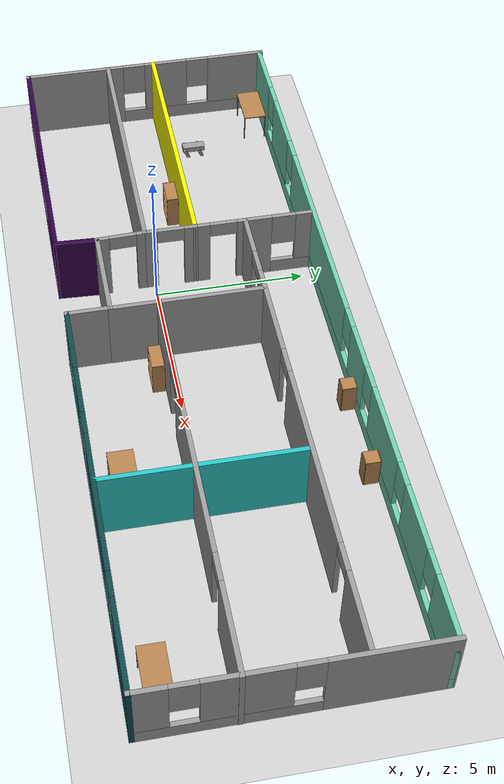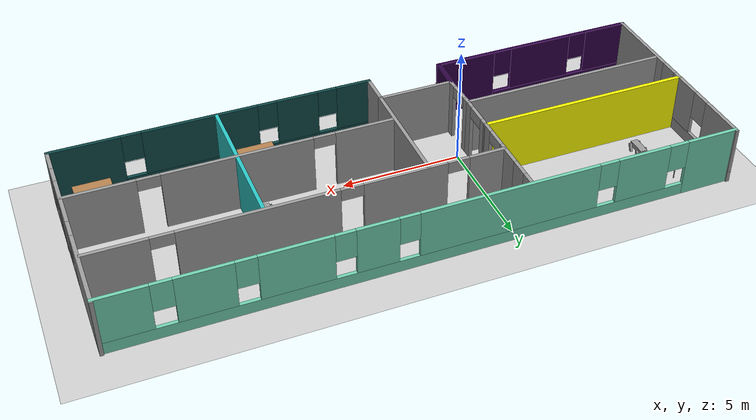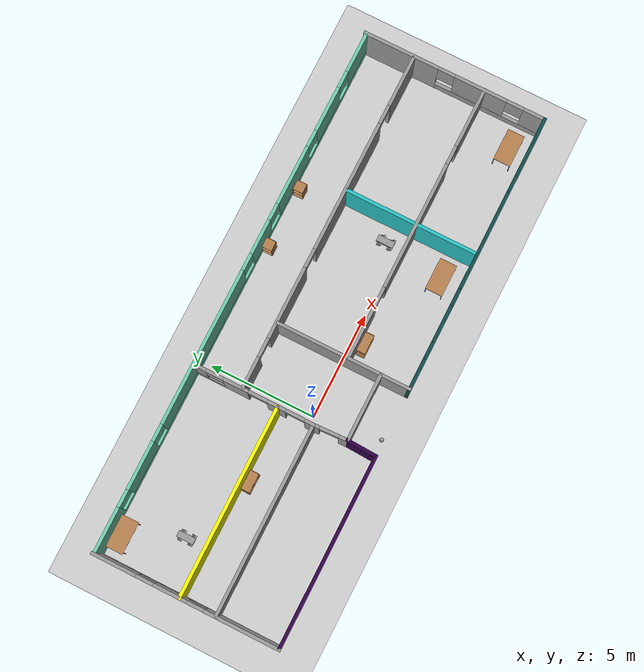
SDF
<sdf version="1.6">
 <world name="default">
  <plugin name="welcome_message" filename="libwelcome_message.so"/>
  <light name="sun" type="directional">
   <pose>0 0 10 0 -0 0</pose>
   <diffuse>0.8 0.8 0.8 1</diffuse>
   <specular>0.2 0.2 0.2 1</specular>
   <attenuation>
    <range>1000</range>
    <constant>0.9</constant>
    <linear>0.01</linear>
    <quadratic>0.001</quadratic>
   </attenuation>
   <direction>-0.5 0.1 -0.9</direction>
  </light>
  <model name="ground_plane">
   <static>1</static>
   <link name="link">
    <collision name="collision">
     <geometry><plane><normal>0 0 1</normal><size>100 100</size></plane></geometry>
     <surface>
      <contact><collide_bitmask>65535</collide_bitmask></contact>
      <friction><ode><mu>100</mu><mu2>50</mu2></ode></friction>
     </surface>
    </collision>
    <visual name="visual">
     <cast_shadows>0</cast_shadows>
     <geometry><plane><normal>0 0 1</normal><size>100 100</size></plane></geometry>
     <material>
      <script><uri>file://media/materials/scripts/gazebo.material</uri><name>Gazebo/Grey</name></script>
     </material>
    </visual>
   </link>
  </model>
  <gravity>0 0 -9.8</gravity>
  <magnetic_field>6e-06 2.3e-05 -4.2e-05</magnetic_field>
  <atmosphere type="adiabatic"/>
  <physics name="default_physics" default="0" type="ode">
   <max_step_size>0.001</max_step_size>
   <real_time_factor>1</real_time_factor>
   <real_time_update_rate>1000</real_time_update_rate>
  </physics>
  <scene><ambient>0.4 0.4 0.4 1</ambient><background>0.7 0.7 0.7 1</background><shadows>1</shadows></scene>
  <spherical_coordinates>
   <surface_model>EARTH_WGS84</surface_model>
   <latitude_deg>0</latitude_deg>
   <longitude_deg>0</longitude_deg>
   <elevation>0</elevation>
   <heading_deg>0</heading_deg>
  </spherical_coordinates>
  <model name="Building">
   <pose>3.20811 1.13485 0 0 -0 0</pose>
   <link name="Wall_10">
    <collision name="Wall_10_Collision">
     <geometry><box><size>1.50133 0.15 2.5</size></box></geometry>
     <pose>0 0 1.25 0 -0 0</pose>
    </collision>
    <visual name="Wall_10_Visual">
     <pose>0 0 1.25 0 -0 0</pose>
     <geometry><box><size>1.50133 0.15 2.5</size></box></geometry>
     <material>
      <script><uri>file://media/materials/scripts/gazebo.material</uri><name>Gazebo/Grey</name></script>
      <ambient>0.184314 0 0.278431 1</ambient>
     </material>
     <meta><layer>0</layer></meta>
    </visual>
    <pose>-3.67596 -3.64047 0 0 0 -1.61521</pose>
   </link>
   <link name="Wall_12">
    <collision name="Wall_12_Collision">
     <geometry><box><size>9 0.15 2.5</size></box></geometry>
     <pose>0 0 1.25 0 -0 0</pose>
    </collision>
    <visual name="Wall_12_Visual">
     <pose>0 0 1.25 0 -0 0</pose>
     <geometry><box><size>9 0.15 2.5</size></box></geometry>
     <material>
      <script><uri>file://media/materials/scripts/gazebo.material</uri><name>Gazebo/Grey</name></script>
      <ambient>1 1 1 1</ambient>
     </material>
     <meta><layer>0</layer></meta>
    </visual>
    <pose>-8.13246 -1.39539 0 0 -0 0</pose>
   </link>
   <link name="Wall_13">
    <pose>-3.67671 -2.18043 0 0 0 -1.53165</pose>
    <visual name="Wall_13_Visual_0">
     <pose>-0.681597 0 1.25 0 -0 0</pose>
     <geometry><box><size>0.35809 0.15 2.5</size></box></geometry>
     <material>
      <script><uri>file://media/materials/scripts/gazebo.material</uri><name>Gazebo/Grey</name></script>
      <ambient>1 1 1 1</ambient>
     </material>
     <meta><layer>0</layer></meta>
    </visual>
    <collision name="Wall_13_Collision_0">
     <geometry><box><size>0.35809 0.15 2.5</size></box></geometry>
     <pose>-0.681597 0 1.25 0 -0 0</pose>
    </collision>
    <visual name="Wall_13_Visual_1">
     <pose>0.629045 0 1.25 0 -0 0</pose>
     <geometry><box><size>0.463193 0.15 2.5</size></box></geometry>
     <material>
      <script><uri>file://media/materials/scripts/gazebo.material</uri><name>Gazebo/Grey</name></script>
      <ambient>1 1 1 1</ambient>
     </material>
     <meta><layer>0</layer></meta>
    </visual>
    <collision name="Wall_13_Collision_1">
     <geometry><box><size>0.463193 0.15 2.5</size></box></geometry>
     <pose>0.629045 0 1.25 0 -0 0</pose>
    </collision>
    <visual name="Wall_13_Visual_2">
     <pose>-0.052551 0 2.25 0 -0 0</pose>
     <geometry><box><size>0.9 0.15 0.5</size></box></geometry>
     <material>
      <script><uri>file://media/materials/scripts/gazebo.material</uri><name>Gazebo/Grey</name></script>
      <ambient>1 1 1 1</ambient>
     </material>
     <meta><layer>0</layer></meta>
    </visual>
    <collision name="Wall_13_Collision_2">
     <geometry><box><size>0.9 0.15 0.5</size></box></geometry>
     <pose>-0.052551 0 2.25 0 -0 0</pose>
    </collision>
   </link>
   <link name="Wall_15">
    <collision name="Wall_15_Collision">
     <geometry><box><size>9 0.15 2.5</size></box></geometry>
     <pose>0 0 1.25 0 -0 0</pose>
    </collision>
    <visual name="Wall_15_Visual">
     <pose>0 0 1.25 0 -0 0</pose>
     <geometry><box><size>9 0.15 2.5</size></box></geometry>
     <material>
      <script><uri>file://media/materials/scripts/gazebo.material</uri><name>Gazebo/Grey</name></script>
      <ambient>1 1 0 1</ambient>
     </material>
     <meta><layer>0</layer></meta>
    </visual>
    <pose>-8.13246 0.277573 0 0 -0 0</pose>
   </link>
   <link name="Wall_16">
    <collision name="Wall_16_Collision">
     <geometry><box><size>0.16 0.15 2.5</size></box></geometry>
     <pose>0 0 1.25 0 -0 0</pose>
    </collision>
    <visual name="Wall_16_Visual">
     <pose>0 0 1.25 0 -0 0</pose>
     <geometry><box><size>0.16 0.15 2.5</size></box></geometry>
     <material>
      <script><uri>file://media/materials/scripts/gazebo.material</uri><name>Gazebo/Grey</name></script>
      <ambient>1 1 1 1</ambient>
     </material>
     <meta><layer>0</layer></meta>
    </visual>
    <pose>-3.70246 0.277573 0 0 -0 0</pose>
   </link>
   <link name="Wall_17">
    <pose>-3.70246 -0.558908 0 0 0 -1.57677</pose>
    <visual name="Wall_17_Visual_0">
     <pose>-0.688342 0 1.25 0 -0 0</pose>
     <geometry><box><size>0.446309 0.15 2.5</size></box></geometry>
     <material>
      <script><uri>file://media/materials/scripts/gazebo.material</uri><name>Gazebo/Grey</name></script>
      <ambient>1 1 1 1</ambient>
     </material>
     <meta><layer>0</layer></meta>
    </visual>
    <collision name="Wall_17_Collision_0">
     <geometry><box><size>0.446309 0.15 2.5</size></box></geometry>
     <pose>-0.688342 0 1.25 0 -0 0</pose>
    </collision>
    <visual name="Wall_17_Visual_1">
     <pose>0.673154 0 1.25 0 -0 0</pose>
     <geometry><box><size>0.476684 0.15 2.5</size></box></geometry>
     <material>
      <script><uri>file://media/materials/scripts/gazebo.material</uri><name>Gazebo/Grey</name></script>
      <ambient>1 1 1 1</ambient>
     </material>
     <meta><layer>0</layer></meta>
    </visual>
    <collision name="Wall_17_Collision_1">
     <geometry><box><size>0.476684 0.15 2.5</size></box></geometry>
     <pose>0.673154 0 1.25 0 -0 0</pose>
    </collision>
    <visual name="Wall_17_Visual_2">
     <pose>-0.015188 0 2.25 0 -0 0</pose>
     <geometry><box><size>0.9 0.15 0.5</size></box></geometry>
     <material>
      <script><uri>file://media/materials/scripts/gazebo.material</uri><name>Gazebo/Grey</name></script>
      <ambient>1 1 1 1</ambient>
     </material>
     <meta><layer>0</layer></meta>
    </visual>
    <collision name="Wall_17_Collision_2">
     <geometry><box><size>0.9 0.15 0.5</size></box></geometry>
     <pose>-0.015188 0 2.25 0 -0 0</pose>
    </collision>
   </link>
   <link name="Wall_19">
    <pose>-3.69746 2.20257 0 0 -0 1.5708</pose>
    <visual name="Wall_19_Visual_0">
     <pose>-1.71603 0 1.25 0 -0 0</pose>
     <geometry><box><size>0.567942 0.15 2.5</size></box></geometry>
     <material>
      <script><uri>file://media/materials/scripts/gazebo.material</uri><name>Gazebo/Grey</name></script>
      <ambient>1 1 1 1</ambient>
     </material>
     <meta><layer>0</layer></meta>
    </visual>
    <collision name="Wall_19_Collision_0">
     <geometry><box><size>0.567942 0.15 2.5</size></box></geometry>
     <pose>-1.71603 0 1.25 0 -0 0</pose>
    </collision>
    <visual name="Wall_19_Visual_1">
     <pose>0.057167 0 1.25 0 -0 0</pose>
     <geometry><box><size>1.17845 0.15 2.5</size></box></geometry>
     <material>
      <script><uri>file://media/materials/scripts/gazebo.material</uri><name>Gazebo/Grey</name></script>
      <ambient>1 1 1 1</ambient>
     </material>
     <meta><layer>0</layer></meta>
    </visual>
    <collision name="Wall_19_Collision_1">
     <geometry><box><size>1.17845 0.15 2.5</size></box></geometry>
     <pose>0.057167 0 1.25 0 -0 0</pose>
    </collision>
    <visual name="Wall_19_Visual_2">
     <pose>1.32319 0 0.25 0 -0 0</pose>
     <geometry><box><size>1.35361 0.15 0.5</size></box></geometry>
     <material>
      <script><uri>file://media/materials/scripts/gazebo.material</uri><name>Gazebo/Grey</name></script>
      <ambient>1 1 1 1</ambient>
     </material>
     <meta><layer>0</layer></meta>
    </visual>
    <collision name="Wall_19_Collision_2">
     <geometry><box><size>1.35361 0.15 0.5</size></box></geometry>
     <pose>1.32319 0 0.25 0 -0 0</pose>
    </collision>
    <visual name="Wall_19_Visual_3">
     <pose>1.7232 0 1.5 0 -0 0</pose>
     <geometry><box><size>0.553609 0.15 2</size></box></geometry>
     <material>
      <script><uri>file://media/materials/scripts/gazebo.material</uri><name>Gazebo/Grey</name></script>
      <ambient>1 1 1 1</ambient>
     </material>
     <meta><layer>0</layer></meta>
    </visual>
    <collision name="Wall_19_Collision_3">
     <geometry><box><size>0.553609 0.15 2</size></box></geometry>
     <pose>1.7232 0 1.5 0 -0 0</pose>
    </collision>
    <visual name="Wall_19_Visual_4">
     <pose>1.04639 0 1.9 0 -0 0</pose>
     <geometry><box><size>0.8 0.15 1.2</size></box></geometry>
     <material>
      <script><uri>file://media/materials/scripts/gazebo.material</uri><name>Gazebo/Grey</name></script>
      <ambient>1 1 1 1</ambient>
     </material>
     <meta><layer>0</layer></meta>
    </visual>
    <collision name="Wall_19_Collision_4">
     <geometry><box><size>0.8 0.15 1.2</size></box></geometry>
     <pose>1.04639 0 1.9 0 -0 0</pose>
    </collision>
    <visual name="Wall_19_Visual_5">
     <pose>-0.982058 0 2.25 0 -0 0</pose>
     <geometry><box><size>0.9 0.15 0.5</size></box></geometry>
     <material>
      <script><uri>file://media/materials/scripts/gazebo.material</uri><name>Gazebo/Grey</name></script>
      <ambient>1 1 1 1</ambient>
     </material>
     <meta><layer>0</layer></meta>
    </visual>
    <collision name="Wall_19_Collision_5">
     <geometry><box><size>0.9 0.15 0.5</size></box></geometry>
     <pose>-0.982058 0 2.25 0 -0 0</pose>
    </collision>
   </link>
   <link name="Wall_2">
    <pose>-8.13096 -4.31547 0 0 -0 3.14159</pose>
    <visual name="Wall_2_Visual_0">
     <pose>-3.17905 0 1.25 0 -0 0</pose>
     <geometry><box><size>2.6419 0.15 2.5</size></box></geometry>
     <material>
      <script><uri>file://media/materials/scripts/gazebo.material</uri><name>Gazebo/Grey</name></script>
      <ambient>0.184314 0 0.278431 1</ambient>
     </material>
     <meta><layer>0</layer></meta>
    </visual>
    <collision name="Wall_2_Collision_0">
     <geometry><box><size>2.6419 0.15 2.5</size></box></geometry>
     <pose>-3.17905 0 1.25 0 -0 0</pose>
    </collision>
    <visual name="Wall_2_Visual_1">
     <pose>1.32095 0 0.25 0 -0 0</pose>
     <geometry><box><size>6.3581 0.15 0.5</size></box></geometry>
     <material>
      <script><uri>file://media/materials/scripts/gazebo.material</uri><name>Gazebo/Grey</name></script>
      <ambient>0.184314 0 0.278431 1</ambient>
     </material>
     <meta><layer>0</layer></meta>
    </visual>
    <collision name="Wall_2_Collision_1">
     <geometry><box><size>6.3581 0.15 0.5</size></box></geometry>
     <pose>1.32095 0 0.25 0 -0 0</pose>
    </collision>
    <visual name="Wall_2_Visual_2">
     <pose>0.346089 0 1.5 0 -0 0</pose>
     <geometry><box><size>2.80837 0.15 2</size></box></geometry>
     <material>
      <script><uri>file://media/materials/scripts/gazebo.material</uri><name>Gazebo/Grey</name></script>
      <ambient>0.184314 0 0.278431 1</ambient>
     </material>
     <meta><layer>0</layer></meta>
    </visual>
    <collision name="Wall_2_Collision_2">
     <geometry><box><size>2.80837 0.15 2</size></box></geometry>
     <pose>0.346089 0 1.5 0 -0 0</pose>
    </collision>
    <visual name="Wall_2_Visual_3">
     <pose>3.52514 0 1.5 0 -0 0</pose>
     <geometry><box><size>1.94972 0.15 2</size></box></geometry>
     <material>
      <script><uri>file://media/materials/scripts/gazebo.material</uri><name>Gazebo/Grey</name></script>
      <ambient>0.184314 0 0.278431 1</ambient>
     </material>
     <meta><layer>0</layer></meta>
    </visual>
    <collision name="Wall_2_Collision_3">
     <geometry><box><size>1.94972 0.15 2</size></box></geometry>
     <pose>3.52514 0 1.5 0 -0 0</pose>
    </collision>
    <visual name="Wall_2_Visual_4">
     <pose>-1.4581 0 1.9 0 -0 0</pose>
     <geometry><box><size>0.8 0.15 1.2</size></box></geometry>
     <material>
      <script><uri>file://media/materials/scripts/gazebo.material</uri><name>Gazebo/Grey</name></script>
      <ambient>0.184314 0 0.278431 1</ambient>
     </material>
     <meta><layer>0</layer></meta>
    </visual>
    <collision name="Wall_2_Collision_4">
     <geometry><box><size>0.8 0.15 1.2</size></box></geometry>
     <pose>-1.4581 0 1.9 0 -0 0</pose>
    </collision>
    <visual name="Wall_2_Visual_5">
     <pose>2.15028 0 1.9 0 -0 0</pose>
     <geometry><box><size>0.8 0.15 1.2</size></box></geometry>
     <material>
      <script><uri>file://media/materials/scripts/gazebo.material</uri><name>Gazebo/Grey</name></script>
      <ambient>0.184314 0 0.278431 1</ambient>
     </material>
     <meta><layer>0</layer></meta>
    </visual>
    <collision name="Wall_2_Collision_5">
     <geometry><box><size>0.8 0.15 1.2</size></box></geometry>
     <pose>2.15028 0 1.9 0 -0 0</pose>
    </collision>
   </link>
   <link name="Wall_21">
    <collision name="Wall_21_Collision">
     <geometry><box><size>5 0.15 2.5</size></box></geometry>
     <pose>0 0 1.25 0 -0 0</pose>
    </collision>
    <visual name="Wall_21_Visual">
     <pose>0 0 1.25 0 -0 0</pose>
     <geometry><box><size>5 0.15 2.5</size></box></geometry>
     <material>
      <script><uri>file://media/materials/scripts/gazebo.material</uri><name>Gazebo/Grey</name></script>
      <ambient>1 1 1 1</ambient>
     </material>
     <meta><layer>0</layer></meta>
    </visual>
    <pose>-0.545964 -0.54047 0 0 -0 1.5708</pose>
   </link>
   <link name="Wall_24">
    <pose>4.40487 1.95053 0 0 -0 0</pose>
    <visual name="Wall_24_Visual_0">
     <pose>-7.36956 0 1.25 0 -0 0</pose>
     <geometry><box><size>1.51089 0.15 2.5</size></box></geometry>
     <material>
      <script><uri>file://media/materials/scripts/gazebo.material</uri><name>Gazebo/Grey</name></script>
      <ambient>0.580392 0.568627 0.568627 1</ambient>
     </material>
     <meta><layer>0</layer></meta>
    </visual>
    <collision name="Wall_24_Collision_0">
     <geometry><box><size>1.51089 0.15 2.5</size></box></geometry>
     <pose>-7.36956 0 1.25 0 -0 0</pose>
    </collision>
    <visual name="Wall_24_Visual_1">
     <pose>-4.01968 0 1.25 0 -0 0</pose>
     <geometry><box><size>3.38887 0.15 2.5</size></box></geometry>
     <material>
      <script><uri>file://media/materials/scripts/gazebo.material</uri><name>Gazebo/Grey</name></script>
      <ambient>0.580392 0.568627 0.568627 1</ambient>
     </material>
     <meta><layer>0</layer></meta>
    </visual>
    <collision name="Wall_24_Collision_1">
     <geometry><box><size>3.38887 0.15 2.5</size></box></geometry>
     <pose>-4.01968 0 1.25 0 -0 0</pose>
    </collision>
    <visual name="Wall_24_Visual_2">
     <pose>1.66839 0 1.25 0 -0 0</pose>
     <geometry><box><size>6.18728 0.15 2.5</size></box></geometry>
     <material>
      <script><uri>file://media/materials/scripts/gazebo.material</uri><name>Gazebo/Grey</name></script>
      <ambient>0.580392 0.568627 0.568627 1</ambient>
     </material>
     <meta><layer>0</layer></meta>
    </visual>
    <collision name="Wall_24_Collision_2">
     <geometry><box><size>6.18728 0.15 2.5</size></box></geometry>
     <pose>1.66839 0 1.25 0 -0 0</pose>
    </collision>
    <visual name="Wall_24_Visual_3">
     <pose>6.89351 0 1.25 0 -0 0</pose>
     <geometry><box><size>2.46297 0.15 2.5</size></box></geometry>
     <material>
      <script><uri>file://media/materials/scripts/gazebo.material</uri><name>Gazebo/Grey</name></script>
      <ambient>0.580392 0.568627 0.568627 1</ambient>
     </material>
     <meta><layer>0</layer></meta>
    </visual>
    <collision name="Wall_24_Collision_3">
     <geometry><box><size>2.46297 0.15 2.5</size></box></geometry>
     <pose>6.89351 0 1.25 0 -0 0</pose>
    </collision>
    <visual name="Wall_24_Visual_4">
     <pose>-6.16411 0 2.25 0 -0 0</pose>
     <geometry><box><size>0.9 0.15 0.5</size></box></geometry>
     <material>
      <script><uri>file://media/materials/scripts/gazebo.material</uri><name>Gazebo/Grey</name></script>
      <ambient>0.580392 0.568627 0.568627 1</ambient>
     </material>
     <meta><layer>0</layer></meta>
    </visual>
    <collision name="Wall_24_Collision_4">
     <geometry><box><size>0.9 0.15 0.5</size></box></geometry>
     <pose>-6.16411 0 2.25 0 -0 0</pose>
    </collision>
    <visual name="Wall_24_Visual_5">
     <pose>-1.87525 0 2.25 0 -0 0</pose>
     <geometry><box><size>0.9 0.15 0.5</size></box></geometry>
     <material>
      <script><uri>file://media/materials/scripts/gazebo.material</uri><name>Gazebo/Grey</name></script>
      <ambient>0.580392 0.568627 0.568627 1</ambient>
     </material>
     <meta><layer>0</layer></meta>
    </visual>
    <collision name="Wall_24_Collision_5">
     <geometry><box><size>0.9 0.15 0.5</size></box></geometry>
     <pose>-1.87525 0 2.25 0 -0 0</pose>
    </collision>
    <visual name="Wall_24_Visual_6">
     <pose>5.21203 0 2.25 0 -0 0</pose>
     <geometry><box><size>0.9 0.15 0.5</size></box></geometry>
     <material>
      <script><uri>file://media/materials/scripts/gazebo.material</uri><name>Gazebo/Grey</name></script>
      <ambient>0.580392 0.568627 0.568627 1</ambient>
     </material>
     <meta><layer>0</layer></meta>
    </visual>
    <collision name="Wall_24_Collision_6">
     <geometry><box><size>0.9 0.15 0.5</size></box></geometry>
     <pose>5.21203 0 2.25 0 -0 0</pose>
    </collision>
   </link>
   <link name="Wall_26">
    <pose>6.00746 -1.42581 0 0 -0 0</pose>
    <visual name="Wall_26_Visual_0">
     <pose>-5.33725 0 1.25 0 -0 0</pose>
     <geometry><box><size>2.5755 0.15 2.5</size></box></geometry>
     <material>
      <script><uri>file://media/materials/scripts/gazebo.material</uri><name>Gazebo/Grey</name></script>
      <ambient>0.580392 0.568627 0.568627 1</ambient>
     </material>
     <meta><layer>0</layer></meta>
    </visual>
    <collision name="Wall_26_Collision_0">
     <geometry><box><size>2.5755 0.15 2.5</size></box></geometry>
     <pose>-5.33725 0 1.25 0 -0 0</pose>
    </collision>
    <visual name="Wall_26_Visual_1">
     <pose>-0.147116 0 1.25 0 -0 0</pose>
     <geometry><box><size>6.00477 0.15 2.5</size></box></geometry>
     <material>
      <script><uri>file://media/materials/scripts/gazebo.material</uri><name>Gazebo/Grey</name></script>
      <ambient>0.580392 0.568627 0.568627 1</ambient>
     </material>
     <meta><layer>0</layer></meta>
    </visual>
    <collision name="Wall_26_Collision_1">
     <geometry><box><size>6.00477 0.15 2.5</size></box></geometry>
     <pose>-0.147116 0 1.25 0 -0 0</pose>
    </collision>
    <visual name="Wall_26_Visual_2">
     <pose>5.19013 0 1.25 0 -0 0</pose>
     <geometry><box><size>2.86973 0.15 2.5</size></box></geometry>
     <material>
      <script><uri>file://media/materials/scripts/gazebo.material</uri><name>Gazebo/Grey</name></script>
      <ambient>0.580392 0.568627 0.568627 1</ambient>
     </material>
     <meta><layer>0</layer></meta>
    </visual>
    <collision name="Wall_26_Collision_2">
     <geometry><box><size>2.86973 0.15 2.5</size></box></geometry>
     <pose>5.19013 0 1.25 0 -0 0</pose>
    </collision>
    <visual name="Wall_26_Visual_3">
     <pose>-3.5995 0 2.25 0 -0 0</pose>
     <geometry><box><size>0.9 0.15 0.5</size></box></geometry>
     <material>
      <script><uri>file://media/materials/scripts/gazebo.material</uri><name>Gazebo/Grey</name></script>
      <ambient>0.580392 0.568627 0.568627 1</ambient>
     </material>
     <meta><layer>0</layer></meta>
    </visual>
    <collision name="Wall_26_Collision_3">
     <geometry><box><size>0.9 0.15 0.5</size></box></geometry>
     <pose>-3.5995 0 2.25 0 -0 0</pose>
    </collision>
    <visual name="Wall_26_Visual_4">
     <pose>3.30527 0 2.25 0 -0 0</pose>
     <geometry><box><size>0.9 0.15 0.5</size></box></geometry>
     <material>
      <script><uri>file://media/materials/scripts/gazebo.material</uri><name>Gazebo/Grey</name></script>
      <ambient>0.580392 0.568627 0.568627 1</ambient>
     </material>
     <meta><layer>0</layer></meta>
    </visual>
    <collision name="Wall_26_Collision_4">
     <geometry><box><size>0.9 0.15 0.5</size></box></geometry>
     <pose>3.30527 0 2.25 0 -0 0</pose>
    </collision>
   </link>
   <link name="Wall_28">
    <collision name="Wall_28_Collision">
     <geometry><box><size>6.25 0.15 2.5</size></box></geometry>
     <pose>0 0 1.25 0 -0 0</pose>
    </collision>
    <visual name="Wall_28_Visual">
     <pose>0 0 1.25 0 -0 0</pose>
     <geometry><box><size>6.25 0.15 2.5</size></box></geometry>
     <material>
      <script><uri>file://media/materials/scripts/gazebo.material</uri><name>Gazebo/Grey</name></script>
      <ambient>0.164706 0.760784 0.760784 1</ambient>
     </material>
     <meta><layer>0</layer></meta>
    </visual>
    <pose>5.90597 -1.20115 0 0 0 -1.5708</pose>
   </link>
   <link name="Wall_3">
    <pose>-12.556 0.001628 0 0 -0 1.5708</pose>
    <visual name="Wall_3_Visual_0">
     <pose>-2.62283 0 1.25 0 -0 0</pose>
     <geometry><box><size>3.53854 0.15 2.5</size></box></geometry>
     <material>
      <script><uri>file://media/materials/scripts/gazebo.material</uri><name>Gazebo/Grey</name></script>
      <ambient>1 1 1 1</ambient>
     </material>
     <meta><layer>0</layer></meta>
    </visual>
    <collision name="Wall_3_Collision_0">
     <geometry><box><size>3.53854 0.15 2.5</size></box></geometry>
     <pose>-2.62283 0 1.25 0 -0 0</pose>
    </collision>
    <visual name="Wall_3_Visual_1">
     <pose>1.76927 0 0.25 0 -0 0</pose>
     <geometry><box><size>5.24566 0.15 0.5</size></box></geometry>
     <material>
      <script><uri>file://media/materials/scripts/gazebo.material</uri><name>Gazebo/Grey</name></script>
      <ambient>1 1 1 1</ambient>
     </material>
     <meta><layer>0</layer></meta>
    </visual>
    <collision name="Wall_3_Collision_1">
     <geometry><box><size>5.24566 0.15 0.5</size></box></geometry>
     <pose>1.76927 0 0.25 0 -0 0</pose>
    </collision>
    <visual name="Wall_3_Visual_2">
     <pose>0.7261 0 1.5 0 -0 0</pose>
     <geometry><box><size>1.55932 0.15 2</size></box></geometry>
     <material>
      <script><uri>file://media/materials/scripts/gazebo.material</uri><name>Gazebo/Grey</name></script>
      <ambient>1 1 1 1</ambient>
     </material>
     <meta><layer>0</layer></meta>
    </visual>
    <collision name="Wall_3_Collision_2">
     <geometry><box><size>1.55932 0.15 2</size></box></geometry>
     <pose>0.7261 0 1.5 0 -0 0</pose>
    </collision>
    <visual name="Wall_3_Visual_3">
     <pose>3.34893 0 1.5 0 -0 0</pose>
     <geometry><box><size>2.08634 0.15 2</size></box></geometry>
     <material>
      <script><uri>file://media/materials/scripts/gazebo.material</uri><name>Gazebo/Grey</name></script>
      <ambient>1 1 1 1</ambient>
     </material>
     <meta><layer>0</layer></meta>
    </visual>
    <collision name="Wall_3_Collision_3">
     <geometry><box><size>2.08634 0.15 2</size></box></geometry>
     <pose>3.34893 0 1.5 0 -0 0</pose>
    </collision>
    <visual name="Wall_3_Visual_4">
     <pose>-0.453561 0 1.9 0 -0 0</pose>
     <geometry><box><size>0.8 0.15 1.2</size></box></geometry>
     <material>
      <script><uri>file://media/materials/scripts/gazebo.material</uri><name>Gazebo/Grey</name></script>
      <ambient>1 1 1 1</ambient>
     </material>
     <meta><layer>0</layer></meta>
    </visual>
    <collision name="Wall_3_Collision_4">
     <geometry><box><size>0.8 0.15 1.2</size></box></geometry>
     <pose>-0.453561 0 1.9 0 -0 0</pose>
    </collision>
    <visual name="Wall_3_Visual_5">
     <pose>1.90576 0 1.9 0 -0 0</pose>
     <geometry><box><size>0.8 0.15 1.2</size></box></geometry>
     <material>
      <script><uri>file://media/materials/scripts/gazebo.material</uri><name>Gazebo/Grey</name></script>
      <ambient>1 1 1 1</ambient>
     </material>
     <meta><layer>0</layer></meta>
    </visual>
    <collision name="Wall_3_Collision_5">
     <geometry><box><size>0.8 0.15 1.2</size></box></geometry>
     <pose>1.90576 0 1.9 0 -0 0</pose>
    </collision>
   </link>
   <link name="Wall_4">
    <pose>-0.005964 4.25789 0 0 -0 0</pose>
    <visual name="Wall_4_Visual_0">
     <pose>-11.5114 0 1.25 0 -0 0</pose>
     <geometry><box><size>2.22729 0.15 2.5</size></box></geometry>
     <material>
      <script><uri>file://media/materials/scripts/gazebo.material</uri><name>Gazebo/Grey</name></script>
      <ambient>0.435294 0.796078 0.67451 1</ambient>
     </material>
     <meta><layer>0</layer></meta>
    </visual>
    <collision name="Wall_4_Collision_0">
     <geometry><box><size>2.22729 0.15 2.5</size></box></geometry>
     <pose>-11.5114 0 1.25 0 -0 0</pose>
    </collision>
    <visual name="Wall_4_Visual_1">
     <pose>1.11365 0 0.25 0 -0 0</pose>
     <geometry><box><size>23.0227 0.15 0.5</size></box></geometry>
     <material>
      <script><uri>file://media/materials/scripts/gazebo.material</uri><name>Gazebo/Grey</name></script>
      <ambient>0.435294 0.796078 0.67451 1</ambient>
     </material>
     <meta><layer>0</layer></meta>
    </visual>
    <collision name="Wall_4_Collision_1">
     <geometry><box><size>23.0227 0.15 0.5</size></box></geometry>
     <pose>1.11365 0 0.25 0 -0 0</pose>
    </collision>
    <visual name="Wall_4_Visual_2">
     <pose>-8.47109 0 1.5 0 -0 0</pose>
     <geometry><box><size>2.25324 0.15 2</size></box></geometry>
     <material>
      <script><uri>file://media/materials/scripts/gazebo.material</uri><name>Gazebo/Grey</name></script>
      <ambient>0.435294 0.796078 0.67451 1</ambient>
     </material>
     <meta><layer>0</layer></meta>
    </visual>
    <collision name="Wall_4_Collision_2">
     <geometry><box><size>2.25324 0.15 2</size></box></geometry>
     <pose>-8.47109 0 1.5 0 -0 0</pose>
    </collision>
    <visual name="Wall_4_Visual_3">
     <pose>-2.87348 0 1.5 0 -0 0</pose>
     <geometry><box><size>7.34197 0.15 2</size></box></geometry>
     <material>
      <script><uri>file://media/materials/scripts/gazebo.material</uri><name>Gazebo/Grey</name></script>
      <ambient>0.435294 0.796078 0.67451 1</ambient>
     </material>
     <meta><layer>0</layer></meta>
    </visual>
    <collision name="Wall_4_Collision_3">
     <geometry><box><size>7.34197 0.15 2</size></box></geometry>
     <pose>-2.87348 0 1.5 0 -0 0</pose>
    </collision>
    <visual name="Wall_4_Visual_4">
     <pose>2.42343 0 1.5 0 -0 0</pose>
     <geometry><box><size>1.65184 0.15 2</size></box></geometry>
     <material>
      <script><uri>file://media/materials/scripts/gazebo.material</uri><name>Gazebo/Grey</name></script>
      <ambient>0.435294 0.796078 0.67451 1</ambient>
     </material>
     <meta><layer>0</layer></meta>
    </visual>
    <collision name="Wall_4_Collision_4">
     <geometry><box><size>1.65184 0.15 2</size></box></geometry>
     <pose>2.42343 0 1.5 0 -0 0</pose>
    </collision>
    <visual name="Wall_4_Visual_5">
     <pose>5.45354 0 1.5 0 -0 0</pose>
     <geometry><box><size>2.80837 0.15 2</size></box></geometry>
     <material>
      <script><uri>file://media/materials/scripts/gazebo.material</uri><name>Gazebo/Grey</name></script>
      <ambient>0.435294 0.796078 0.67451 1</ambient>
     </material>
     <meta><layer>0</layer></meta>
    </visual>
    <collision name="Wall_4_Collision_5">
     <geometry><box><size>2.80837 0.15 2</size></box></geometry>
     <pose>5.45354 0 1.5 0 -0 0</pose>
    </collision>
    <visual name="Wall_4_Visual_6">
     <pose>8.73808 0 1.5 0 -0 0</pose>
     <geometry><box><size>2.16072 0.15 2</size></box></geometry>
     <material>
      <script><uri>file://media/materials/scripts/gazebo.material</uri><name>Gazebo/Grey</name></script>
      <ambient>0.435294 0.796078 0.67451 1</ambient>
     </material>
     <meta><layer>0</layer></meta>
    </visual>
    <collision name="Wall_4_Collision_6">
     <geometry><box><size>2.16072 0.15 2</size></box></geometry>
     <pose>8.73808 0 1.5 0 -0 0</pose>
    </collision>
    <visual name="Wall_4_Visual_7">
     <pose>11.6217 0 1.5 0 -0 0</pose>
     <geometry><box><size>2.00656 0.15 2</size></box></geometry>
     <material>
      <script><uri>file://media/materials/scripts/gazebo.material</uri><name>Gazebo/Grey</name></script>
      <ambient>0.435294 0.796078 0.67451 1</ambient>
     </material>
     <meta><layer>0</layer></meta>
    </visual>
    <collision name="Wall_4_Collision_7">
     <geometry><box><size>2.00656 0.15 2</size></box></geometry>
     <pose>11.6217 0 1.5 0 -0 0</pose>
    </collision>
    <visual name="Wall_4_Visual_8">
     <pose>-9.99771 0 1.9 0 -0 0</pose>
     <geometry><box><size>0.8 0.15 1.2</size></box></geometry>
     <material>
      <script><uri>file://media/materials/scripts/gazebo.material</uri><name>Gazebo/Grey</name></script>
      <ambient>0.435294 0.796078 0.67451 1</ambient>
     </material>
     <meta><layer>0</layer></meta>
    </visual>
    <collision name="Wall_4_Collision_8">
     <geometry><box><size>0.8 0.15 1.2</size></box></geometry>
     <pose>-9.99771 0 1.9 0 -0 0</pose>
    </collision>
    <visual name="Wall_4_Visual_9">
     <pose>-6.94447 0 1.9 0 -0 0</pose>
     <geometry><box><size>0.8 0.15 1.2</size></box></geometry>
     <material>
      <script><uri>file://media/materials/scripts/gazebo.material</uri><name>Gazebo/Grey</name></script>
      <ambient>0.435294 0.796078 0.67451 1</ambient>
     </material>
     <meta><layer>0</layer></meta>
    </visual>
    <collision name="Wall_4_Collision_9">
     <geometry><box><size>0.8 0.15 1.2</size></box></geometry>
     <pose>-6.94447 0 1.9 0 -0 0</pose>
    </collision>
    <visual name="Wall_4_Visual_10">
     <pose>1.19751 0 1.9 0 -0 0</pose>
     <geometry><box><size>0.8 0.15 1.2</size></box></geometry>
     <material>
      <script><uri>file://media/materials/scripts/gazebo.material</uri><name>Gazebo/Grey</name></script>
      <ambient>0.435294 0.796078 0.67451 1</ambient>
     </material>
     <meta><layer>0</layer></meta>
    </visual>
    <collision name="Wall_4_Collision_10">
     <geometry><box><size>0.8 0.15 1.2</size></box></geometry>
     <pose>1.19751 0 1.9 0 -0 0</pose>
    </collision>
    <visual name="Wall_4_Visual_11">
     <pose>3.64935 0 1.9 0 -0 0</pose>
     <geometry><box><size>0.8 0.15 1.2</size></box></geometry>
     <material>
      <script><uri>file://media/materials/scripts/gazebo.material</uri><name>Gazebo/Grey</name></script>
      <ambient>0.435294 0.796078 0.67451 1</ambient>
     </material>
     <meta><layer>0</layer></meta>
    </visual>
    <collision name="Wall_4_Collision_11">
     <geometry><box><size>0.8 0.15 1.2</size></box></geometry>
     <pose>3.64935 0 1.9 0 -0 0</pose>
    </collision>
    <visual name="Wall_4_Visual_12">
     <pose>7.25772 0 1.9 0 -0 0</pose>
     <geometry><box><size>0.8 0.15 1.2</size></box></geometry>
     <material>
      <script><uri>file://media/materials/scripts/gazebo.material</uri><name>Gazebo/Grey</name></script>
      <ambient>0.435294 0.796078 0.67451 1</ambient>
     </material>
     <meta><layer>0</layer></meta>
    </visual>
    <collision name="Wall_4_Collision_12">
     <geometry><box><size>0.8 0.15 1.2</size></box></geometry>
     <pose>7.25772 0 1.9 0 -0 0</pose>
    </collision>
    <visual name="Wall_4_Visual_13">
     <pose>10.2184 0 1.9 0 -0 0</pose>
     <geometry><box><size>0.8 0.15 1.2</size></box></geometry>
     <material>
      <script><uri>file://media/materials/scripts/gazebo.material</uri><name>Gazebo/Grey</name></script>
      <ambient>0.435294 0.796078 0.67451 1</ambient>
     </material>
     <meta><layer>0</layer></meta>
    </visual>
    <collision name="Wall_4_Collision_13">
     <geometry><box><size>0.8 0.15 1.2</size></box></geometry>
     <pose>10.2184 0 1.9 0 -0 0</pose>
    </collision>
   </link>
   <link name="Wall_5">
    <pose>12.544 0.001628 0 0 0 -1.5708</pose>
    <visual name="Wall_5_Visual_0">
     <pose>-2.58562 0 1.25 0 -0 0</pose>
     <geometry><box><size>3.61296 0.15 2.5</size></box></geometry>
     <material>
      <script><uri>file://media/materials/scripts/gazebo.material</uri><name>Gazebo/Grey</name></script>
      <ambient>0.580392 0.568627 0.568627 1</ambient>
     </material>
     <meta><layer>0</layer></meta>
    </visual>
    <collision name="Wall_5_Collision_0">
     <geometry><box><size>3.61296 0.15 2.5</size></box></geometry>
     <pose>-2.58562 0 1.25 0 -0 0</pose>
    </collision>
    <visual name="Wall_5_Visual_1">
     <pose>1.80648 0 0.25 0 -0 0</pose>
     <geometry><box><size>5.17124 0.15 0.5</size></box></geometry>
     <material>
      <script><uri>file://media/materials/scripts/gazebo.material</uri><name>Gazebo/Grey</name></script>
      <ambient>0.580392 0.568627 0.568627 1</ambient>
     </material>
     <meta><layer>0</layer></meta>
    </visual>
    <collision name="Wall_5_Collision_1">
     <geometry><box><size>5.17124 0.15 0.5</size></box></geometry>
     <pose>1.80648 0 0.25 0 -0 0</pose>
    </collision>
    <visual name="Wall_5_Visual_2">
     <pose>1.26313 0 1.5 0 -0 0</pose>
     <geometry><box><size>2.48455 0.15 2</size></box></geometry>
     <material>
      <script><uri>file://media/materials/scripts/gazebo.material</uri><name>Gazebo/Grey</name></script>
      <ambient>0.580392 0.568627 0.568627 1</ambient>
     </material>
     <meta><layer>0</layer></meta>
    </visual>
    <collision name="Wall_5_Collision_2">
     <geometry><box><size>2.48455 0.15 2</size></box></geometry>
     <pose>1.26313 0 1.5 0 -0 0</pose>
    </collision>
    <visual name="Wall_5_Visual_3">
     <pose>3.84875 0 1.5 0 -0 0</pose>
     <geometry><box><size>1.08669 0.15 2</size></box></geometry>
     <material>
      <script><uri>file://media/materials/scripts/gazebo.material</uri><name>Gazebo/Grey</name></script>
      <ambient>0.580392 0.568627 0.568627 1</ambient>
     </material>
     <meta><layer>0</layer></meta>
    </visual>
    <collision name="Wall_5_Collision_3">
     <geometry><box><size>1.08669 0.15 2</size></box></geometry>
     <pose>3.84875 0 1.5 0 -0 0</pose>
    </collision>
    <visual name="Wall_5_Visual_4">
     <pose>-0.37914 0 1.9 0 -0 0</pose>
     <geometry><box><size>0.8 0.15 1.2</size></box></geometry>
     <material>
      <script><uri>file://media/materials/scripts/gazebo.material</uri><name>Gazebo/Grey</name></script>
      <ambient>0.580392 0.568627 0.568627 1</ambient>
     </material>
     <meta><layer>0</layer></meta>
    </visual>
    <collision name="Wall_5_Collision_4">
     <geometry><box><size>0.8 0.15 1.2</size></box></geometry>
     <pose>-0.37914 0 1.9 0 -0 0</pose>
    </collision>
    <visual name="Wall_5_Visual_5">
     <pose>2.90541 0 1.9 0 -0 0</pose>
     <geometry><box><size>0.8 0.15 1.2</size></box></geometry>
     <material>
      <script><uri>file://media/materials/scripts/gazebo.material</uri><name>Gazebo/Grey</name></script>
      <ambient>0.580392 0.568627 0.568627 1</ambient>
     </material>
     <meta><layer>0</layer></meta>
    </visual>
    <collision name="Wall_5_Collision_5">
     <geometry><box><size>0.8 0.15 1.2</size></box></geometry>
     <pose>2.90541 0 1.9 0 -0 0</pose>
    </collision>
   </link>
   <link name="Wall_6">
    <pose>5.99404 -4.31547 0 0 -0 3.14159</pose>
    <visual name="Wall_6_Visual_0">
     <pose>-5.18224 0 1.25 0 -0 0</pose>
     <geometry><box><size>2.88552 0.15 2.5</size></box></geometry>
     <material>
      <script><uri>file://media/materials/scripts/gazebo.material</uri><name>Gazebo/Grey</name></script>
      <ambient>0.0588235 0.278431 0.278431 1</ambient>
     </material>
     <meta><layer>0</layer></meta>
    </visual>
    <collision name="Wall_6_Collision_0">
     <geometry><box><size>2.88552 0.15 2.5</size></box></geometry>
     <pose>-5.18224 0 1.25 0 -0 0</pose>
    </collision>
    <visual name="Wall_6_Visual_1">
     <pose>1.44276 0 0.25 0 -0 0</pose>
     <geometry><box><size>10.3645 0.15 0.5</size></box></geometry>
     <material>
      <script><uri>file://media/materials/scripts/gazebo.material</uri><name>Gazebo/Grey</name></script>
      <ambient>0.0588235 0.278431 0.278431 1</ambient>
     </material>
     <meta><layer>0</layer></meta>
    </visual>
    <collision name="Wall_6_Collision_1">
     <geometry><box><size>10.3645 0.15 0.5</size></box></geometry>
     <pose>1.44276 0 0.25 0 -0 0</pose>
    </collision>
    <visual name="Wall_6_Visual_2">
     <pose>-0.586938 0 1.5 0 -0 0</pose>
     <geometry><box><size>4.70509 0.15 2</size></box></geometry>
     <material>
      <script><uri>file://media/materials/scripts/gazebo.material</uri><name>Gazebo/Grey</name></script>
      <ambient>0.0588235 0.278431 0.278431 1</ambient>
     </material>
     <meta><layer>0</layer></meta>
    </visual>
    <collision name="Wall_6_Collision_2">
     <geometry><box><size>4.70509 0.15 2</size></box></geometry>
     <pose>-0.586938 0 1.5 0 -0 0</pose>
    </collision>
    <visual name="Wall_6_Visual_3">
     <pose>3.43779 0 1.5 0 -0 0</pose>
     <geometry><box><size>1.74437 0.15 2</size></box></geometry>
     <material>
      <script><uri>file://media/materials/scripts/gazebo.material</uri><name>Gazebo/Grey</name></script>
      <ambient>0.0588235 0.278431 0.278431 1</ambient>
     </material>
     <meta><layer>0</layer></meta>
    </visual>
    <collision name="Wall_6_Collision_3">
     <geometry><box><size>1.74437 0.15 2</size></box></geometry>
     <pose>3.43779 0 1.5 0 -0 0</pose>
    </collision>
    <visual name="Wall_6_Visual_4">
     <pose>5.86749 0 1.5 0 -0 0</pose>
     <geometry><box><size>1.51503 0.15 2</size></box></geometry>
     <material>
      <script><uri>file://media/materials/scripts/gazebo.material</uri><name>Gazebo/Grey</name></script>
      <ambient>0.0588235 0.278431 0.278431 1</ambient>
     </material>
     <meta><layer>0</layer></meta>
    </visual>
    <collision name="Wall_6_Collision_4">
     <geometry><box><size>1.51503 0.15 2</size></box></geometry>
     <pose>5.86749 0 1.5 0 -0 0</pose>
    </collision>
    <visual name="Wall_6_Visual_5">
     <pose>-3.33948 0 1.9 0 -0 0</pose>
     <geometry><box><size>0.8 0.15 1.2</size></box></geometry>
     <material>
      <script><uri>file://media/materials/scripts/gazebo.material</uri><name>Gazebo/Grey</name></script>
      <ambient>0.0588235 0.278431 0.278431 1</ambient>
     </material>
     <meta><layer>0</layer></meta>
    </visual>
    <collision name="Wall_6_Collision_5">
     <geometry><box><size>0.8 0.15 1.2</size></box></geometry>
     <pose>-3.33948 0 1.9 0 -0 0</pose>
    </collision>
    <visual name="Wall_6_Visual_6">
     <pose>2.1656 0 1.9 0 -0 0</pose>
     <geometry><box><size>0.8 0.15 1.2</size></box></geometry>
     <material>
      <script><uri>file://media/materials/scripts/gazebo.material</uri><name>Gazebo/Grey</name></script>
      <ambient>0.0588235 0.278431 0.278431 1</ambient>
     </material>
     <meta><layer>0</layer></meta>
    </visual>
    <collision name="Wall_6_Collision_6">
     <geometry><box><size>0.8 0.15 1.2</size></box></geometry>
     <pose>2.1656 0 1.9 0 -0 0</pose>
    </collision>
    <visual name="Wall_6_Visual_7">
     <pose>4.70997 0 1.9 0 -0 0</pose>
     <geometry><box><size>0.8 0.15 1.2</size></box></geometry>
     <material>
      <script><uri>file://media/materials/scripts/gazebo.material</uri><name>Gazebo/Grey</name></script>
      <ambient>0.0588235 0.278431 0.278431 1</ambient>
     </material>
     <meta><layer>0</layer></meta>
    </visual>
    <collision name="Wall_6_Collision_7">
     <geometry><box><size>0.8 0.15 1.2</size></box></geometry>
     <pose>4.70997 0 1.9 0 -0 0</pose>
    </collision>
   </link>
   <link name="Wall_7">
    <collision name="Wall_7_Collision">
     <geometry><box><size>1.5 0.15 2.5</size></box></geometry>
     <pose>0 0 1.25 0 -0 0</pose>
    </collision>
    <visual name="Wall_7_Visual">
     <pose>0 0 1.25 0 -0 0</pose>
     <geometry><box><size>1.5 0.15 2.5</size></box></geometry>
     <material>
      <script><uri>file://media/materials/scripts/gazebo.material</uri><name>Gazebo/Grey</name></script>
      <ambient>1 1 1 1</ambient>
     </material>
     <meta><layer>0</layer></meta>
    </visual>
    <pose>-0.555964 -3.64047 0 0 -0 1.5708</pose>
   </link>
   <link name="Wall_8">
    <collision name="Wall_8_Collision">
     <geometry><box><size>0.16 0.15 2.5</size></box></geometry>
     <pose>0 0 1.25 0 -0 0</pose>
    </collision>
    <visual name="Wall_8_Visual">
     <pose>0 0 1.25 0 -0 0</pose>
     <geometry><box><size>0.16 0.15 2.5</size></box></geometry>
     <material>
      <script><uri>file://media/materials/scripts/gazebo.material</uri><name>Gazebo/Grey</name></script>
      <ambient>1 1 1 1</ambient>
     </material>
     <meta><layer>0</layer></meta>
    </visual>
    <pose>-0.550964 -2.96547 0 0 -0 0</pose>
   </link>
   <link name="Wall_9">
    <collision name="Wall_9_Collision">
     <geometry><box><size>3.25 0.15 2.5</size></box></geometry>
     <pose>0 0 1.25 0 -0 0</pose>
    </collision>
    <visual name="Wall_9_Visual">
     <pose>0 0 1.25 0 -0 0</pose>
     <geometry><box><size>3.25 0.15 2.5</size></box></geometry>
     <material>
      <script><uri>file://media/materials/scripts/gazebo.material</uri><name>Gazebo/Grey</name></script>
      <ambient>1 1 1 1</ambient>
     </material>
     <meta><layer>0</layer></meta>
    </visual>
    <pose>-2.09596 -2.96547 0 0 -0 3.14159</pose>
   </link>
   <static>1</static>
  </model>
  <model name="Dog_0">
   <link name="link_3">
    <pose>0 0 0.155724 0 -0 0</pose>
    <inertial>
     <mass>1</mass>
     <inertia>
      <ixx>0.166667</ixx>
      <ixy>0</ixy>
      <ixz>0</ixz>
      <iyy>0.166667</iyy>
      <iyz>0</iyz>
      <izz>0.166667</izz>
     </inertia>
    </inertial>
    <visual name="visual">
     <geometry><box><size>0.3 0.8 0.2</size></box></geometry>
     <material>
      <lighting>1</lighting>
      <script><uri>file://media/materials/scripts/gazebo.material</uri><name>Gazebo/Grey</name></script>
      <shader type="pixel"><normal_map>__default__</normal_map></shader>
      <ambient>0.3 0.3 0.3 1</ambient>
      <diffuse>0.7 0.7 0.7 1</diffuse>
      <specular>0.01 0.01 0.01 1</specular>
      <emissive>0 0 0 1</emissive>
     </material>
    </visual>
    <collision name="collision">
     <geometry><box><size>0.3 0.8 0.2</size></box></geometry>
     <surface>
      <friction>
       <ode><mu>1</mu><mu2>1</mu2><fdir1>0 0 0</fdir1><slip1>0</slip1><slip2>0</slip2></ode>
       <torsional>
        <coefficient>1</coefficient>
        <patch_radius>0</patch_radius>
        <surface_radius>0</surface_radius>
        <use_patch_radius>1</use_patch_radius>
        <ode><slip>0</slip></ode>
       </torsional>
      </friction>
      <bounce><restitution_coefficient>0</restitution_coefficient><threshold>1e+06</threshold></bounce>
      <contact>
       <collide_without_contact>0</collide_without_contact>
       <collide_without_contact_bitmask>1</collide_without_contact_bitmask>
       <collide_bitmask>1</collide_bitmask>
       <ode>
        <soft_cfm>0</soft_cfm>
        <soft_erp>0.2</soft_erp>
        <kp>1e+13</kp>
        <kd>1</kd>
        <max_vel>0.01</max_vel>
        <min_depth>0</min_depth>
       </ode>
       <bullet>
        <split_impulse>1</split_impulse>
        <split_impulse_penetration_threshold>-0.01</split_impulse_penetration_threshold>
        <soft_cfm>0</soft_cfm>
        <soft_erp>0.2</soft_erp>
        <kp>1e+13</kp>
        <kd>1</kd>
       </bullet>
      </contact>
     </surface>
    </collision>
   </link>
   <link name="link_4_clone">
    <pose>-0.2 0.250498 -0.038931 2 -0 0</pose>
    <inertial>
     <mass>1</mass>
     <inertia>
      <ixx>0.166667</ixx>
      <ixy>0</ixy>
      <ixz>0</ixz>
      <iyy>0.166667</iyy>
      <iyz>0</iyz>
      <izz>0.166667</izz>
     </inertia>
    </inertial>
    <visual name="visual">
     <geometry><box><size>0.1 0.5 0.1</size></box></geometry>
     <material>
      <lighting>1</lighting>
      <script><uri>file://media/materials/scripts/gazebo.material</uri><name>Gazebo/Grey</name></script>
      <shader type="pixel"><normal_map>__default__</normal_map></shader>
      <ambient>0.3 0.3 0.3 1</ambient>
      <diffuse>0.7 0.7 0.7 1</diffuse>
      <specular>0.01 0.01 0.01 1</specular>
      <emissive>0 0 0 1</emissive>
     </material>
    </visual>
    <collision name="collision">
     <geometry><box><size>0.1 0.5 0.1</size></box></geometry>
     <surface>
      <friction>
       <ode><mu>1</mu><mu2>1</mu2><fdir1>0 0 0</fdir1><slip1>0</slip1><slip2>0</slip2></ode>
       <torsional>
        <coefficient>1</coefficient>
        <patch_radius>0</patch_radius>
        <surface_radius>0</surface_radius>
        <use_patch_radius>1</use_patch_radius>
        <ode><slip>0</slip></ode>
       </torsional>
      </friction>
      <bounce><restitution_coefficient>0</restitution_coefficient><threshold>1e+06</threshold></bounce>
      <contact>
       <collide_without_contact>0</collide_without_contact>
       <collide_without_contact_bitmask>1</collide_without_contact_bitmask>
       <collide_bitmask>1</collide_bitmask>
       <ode>
        <soft_cfm>0</soft_cfm>
        <soft_erp>0.2</soft_erp>
        <kp>1e+13</kp>
        <kd>1</kd>
        <max_vel>0.01</max_vel>
        <min_depth>0</min_depth>
       </ode>
       <bullet>
        <split_impulse>1</split_impulse>
        <split_impulse_penetration_threshold>-0.01</split_impulse_penetration_threshold>
        <soft_cfm>0</soft_cfm>
        <soft_erp>0.2</soft_erp>
        <kp>1e+13</kp>
        <kd>1</kd>
       </bullet>
      </contact>
     </surface>
    </collision>
   </link>
   <link name="link_4_clone_0">
    <pose>0.2 -0.250498 -0.038931 2 -0 0</pose>
    <inertial>
     <mass>1</mass>
     <inertia>
      <ixx>0.166667</ixx>
      <ixy>0</ixy>
      <ixz>0</ixz>
      <iyy>0.166667</iyy>
      <iyz>0</iyz>
      <izz>0.166667</izz>
     </inertia>
    </inertial>
    <visual name="visual">
     <geometry><box><size>0.1 0.5 0.1</size></box></geometry>
     <material>
      <lighting>1</lighting>
      <script><uri>file://media/materials/scripts/gazebo.material</uri><name>Gazebo/Grey</name></script>
      <shader type="pixel"><normal_map>__default__</normal_map></shader>
      <ambient>0.3 0.3 0.3 1</ambient>
      <diffuse>0.7 0.7 0.7 1</diffuse>
      <specular>0.01 0.01 0.01 1</specular>
      <emissive>0 0 0 1</emissive>
     </material>
    </visual>
    <collision name="collision">
     <geometry><box><size>0.1 0.5 0.1</size></box></geometry>
     <surface>
      <friction>
       <ode><mu>1</mu><mu2>1</mu2><fdir1>0 0 0</fdir1><slip1>0</slip1><slip2>0</slip2></ode>
       <torsional>
        <coefficient>1</coefficient>
        <patch_radius>0</patch_radius>
        <surface_radius>0</surface_radius>
        <use_patch_radius>1</use_patch_radius>
        <ode><slip>0</slip></ode>
       </torsional>
      </friction>
      <bounce><restitution_coefficient>0</restitution_coefficient><threshold>1e+06</threshold></bounce>
      <contact>
       <collide_without_contact>0</collide_without_contact>
       <collide_without_contact_bitmask>1</collide_without_contact_bitmask>
       <collide_bitmask>1</collide_bitmask>
       <ode>
        <soft_cfm>0</soft_cfm>
        <soft_erp>0.2</soft_erp>
        <kp>1e+13</kp>
        <kd>1</kd>
        <max_vel>0.01</max_vel>
        <min_depth>0</min_depth>
       </ode>
       <bullet>
        <split_impulse>1</split_impulse>
        <split_impulse_penetration_threshold>-0.01</split_impulse_penetration_threshold>
        <soft_cfm>0</soft_cfm>
        <soft_erp>0.2</soft_erp>
        <kp>1e+13</kp>
        <kd>1</kd>
       </bullet>
      </contact>
     </surface>
    </collision>
   </link>
   <link name="link_4_clone_1">
    <pose>-0.2 -0.250498 -0.038931 2 -0 0</pose>
    <inertial>
     <mass>1</mass>
     <inertia>
      <ixx>0.166667</ixx>
      <ixy>0</ixy>
      <ixz>0</ixz>
      <iyy>0.166667</iyy>
      <iyz>0</iyz>
      <izz>0.166667</izz>
     </inertia>
    </inertial>
    <visual name="visual">
     <geometry><box><size>0.1 0.5 0.1</size></box></geometry>
     <material>
      <lighting>1</lighting>
      <script><uri>file://media/materials/scripts/gazebo.material</uri><name>Gazebo/Grey</name></script>
      <shader type="pixel"><normal_map>__default__</normal_map></shader>
      <ambient>0.3 0.3 0.3 1</ambient>
      <diffuse>0.7 0.7 0.7 1</diffuse>
      <specular>0.01 0.01 0.01 1</specular>
      <emissive>0 0 0 1</emissive>
     </material>
    </visual>
    <collision name="collision">
     <geometry><box><size>0.1 0.5 0.1</size></box></geometry>
     <surface>
      <friction>
       <ode><mu>1</mu><mu2>1</mu2><fdir1>0 0 0</fdir1><slip1>0</slip1><slip2>0</slip2></ode>
       <torsional>
        <coefficient>1</coefficient>
        <patch_radius>0</patch_radius>
        <surface_radius>0</surface_radius>
        <use_patch_radius>1</use_patch_radius>
        <ode><slip>0</slip></ode>
       </torsional>
      </friction>
      <bounce><restitution_coefficient>0</restitution_coefficient><threshold>1e+06</threshold></bounce>
      <contact>
       <collide_without_contact>0</collide_without_contact>
       <collide_without_contact_bitmask>1</collide_without_contact_bitmask>
       <collide_bitmask>1</collide_bitmask>
       <ode>
        <soft_cfm>0</soft_cfm>
        <soft_erp>0.2</soft_erp>
        <kp>1e+13</kp>
        <kd>1</kd>
        <max_vel>0.01</max_vel>
        <min_depth>0</min_depth>
       </ode>
       <bullet>
        <split_impulse>1</split_impulse>
        <split_impulse_penetration_threshold>-0.01</split_impulse_penetration_threshold>
        <soft_cfm>0</soft_cfm>
        <soft_erp>0.2</soft_erp>
        <kp>1e+13</kp>
        <kd>1</kd>
       </bullet>
      </contact>
     </surface>
    </collision>
   </link>
   <link name="link_4_clone_1_clone">
    <pose>0.2 0.250498 -0.038931 2 -0 0</pose>
    <inertial>
     <mass>1</mass>
     <inertia>
      <ixx>0.166667</ixx>
      <ixy>0</ixy>
      <ixz>0</ixz>
      <iyy>0.166667</iyy>
      <iyz>0</iyz>
      <izz>0.166667</izz>
     </inertia>
    </inertial>
    <visual name="visual">
     <geometry><box><size>0.1 0.5 0.1</size></box></geometry>
     <material>
      <lighting>1</lighting>
      <script><uri>file://media/materials/scripts/gazebo.material</uri><name>Gazebo/Grey</name></script>
      <shader type="pixel"><normal_map>__default__</normal_map></shader>
      <ambient>0.3 0.3 0.3 1</ambient>
      <diffuse>0.7 0.7 0.7 1</diffuse>
      <specular>0.01 0.01 0.01 1</specular>
      <emissive>0 0 0 1</emissive>
     </material>
    </visual>
    <collision name="collision">
     <geometry><box><size>0.1 0.5 0.1</size></box></geometry>
     <surface>
      <friction>
       <ode><mu>1</mu><mu2>1</mu2><fdir1>0 0 0</fdir1><slip1>0</slip1><slip2>0</slip2></ode>
       <torsional>
        <coefficient>1</coefficient>
        <patch_radius>0</patch_radius>
        <surface_radius>0</surface_radius>
        <use_patch_radius>1</use_patch_radius>
        <ode><slip>0</slip></ode>
       </torsional>
      </friction>
      <bounce><restitution_coefficient>0</restitution_coefficient><threshold>1e+06</threshold></bounce>
      <contact>
       <collide_without_contact>0</collide_without_contact>
       <collide_without_contact_bitmask>1</collide_without_contact_bitmask>
       <collide_bitmask>1</collide_bitmask>
       <ode>
        <soft_cfm>0</soft_cfm>
        <soft_erp>0.2</soft_erp>
        <kp>1e+13</kp>
        <kd>1</kd>
        <max_vel>0.01</max_vel>
        <min_depth>0</min_depth>
       </ode>
       <bullet>
        <split_impulse>1</split_impulse>
        <split_impulse_penetration_threshold>-0.01</split_impulse_penetration_threshold>
        <soft_cfm>0</soft_cfm>
        <soft_erp>0.2</soft_erp>
        <kp>1e+13</kp>
        <kd>1</kd>
       </bullet>
      </contact>
     </surface>
    </collision>
   </link>
   <joint name="link_3_JOINT_1" type="revolute">
    <parent>link_3</parent>
    <child>link_4_clone_0</child>
    <axis>
     <xyz>1 0 0</xyz>
     <use_parent_model_frame>0</use_parent_model_frame>
     <limit>
      <lower>-1.79769e+308</lower>
      <upper>1.79769e+308</upper>
      <effort>-1</effort>
      <velocity>-1</velocity>
     </limit>
     <dynamics>
      <spring_reference>0</spring_reference>
      <spring_stiffness>0</spring_stiffness>
      <damping>0</damping>
     </dynamics>
    </axis>
    <physics>
     <ode><limit><cfm>0</cfm><erp>0.2</erp></limit><suspension><cfm>0</cfm><erp>0.2</erp></suspension></ode>
    </physics>
   </joint>
   <joint name="link_3_JOINT_3" type="revolute">
    <parent>link_3</parent>
    <child>link_4_clone_1_clone</child>
    <axis>
     <xyz>1 0 0</xyz>
     <use_parent_model_frame>0</use_parent_model_frame>
     <limit>
      <lower>-1.79769e+308</lower>
      <upper>1.79769e+308</upper>
      <effort>-1</effort>
      <velocity>-1</velocity>
     </limit>
     <dynamics>
      <spring_reference>0</spring_reference>
      <spring_stiffness>0</spring_stiffness>
      <damping>0</damping>
     </dynamics>
    </axis>
    <physics>
     <ode><limit><cfm>0</cfm><erp>0.2</erp></limit><suspension><cfm>0</cfm><erp>0.2</erp></suspension></ode>
    </physics>
   </joint>
   <joint name="link_3_JOINT_4" type="revolute">
    <parent>link_3</parent>
    <child>link_4_clone</child>
    <axis>
     <xyz>1 0 0</xyz>
     <use_parent_model_frame>0</use_parent_model_frame>
     <limit>
      <lower>-1.79769e+308</lower>
      <upper>1.79769e+308</upper>
      <effort>-1</effort>
      <velocity>-1</velocity>
     </limit>
     <dynamics>
      <spring_reference>0</spring_reference>
      <spring_stiffness>0</spring_stiffness>
      <damping>0</damping>
     </dynamics>
    </axis>
    <physics>
     <ode><limit><cfm>0</cfm><erp>0.2</erp></limit><suspension><cfm>0</cfm><erp>0.2</erp></suspension></ode>
    </physics>
   </joint>
   <joint name="link_3_JOINT_5" type="revolute">
    <parent>link_3</parent>
    <child>link_4_clone_1</child>
    <axis>
     <xyz>1 0 0</xyz>
     <use_parent_model_frame>0</use_parent_model_frame>
     <limit>
      <lower>-1.79769e+308</lower>
      <upper>1.79769e+308</upper>
      <effort>-1</effort>
      <velocity>-1</velocity>
     </limit>
     <dynamics>
      <spring_reference>0</spring_reference>
      <spring_stiffness>0</spring_stiffness>
      <damping>0</damping>
     </dynamics>
    </axis>
    <physics>
     <ode><limit><cfm>0</cfm><erp>0.2</erp></limit><suspension><cfm>0</cfm><erp>0.2</erp></suspension></ode>
    </physics>
   </joint>
   <static>0</static>
   <pose>-7.06317 2.5014 0.088931 0 -0 0.001938</pose>
  </model>
  <model name="Dog_0_clone">
   <link name="link_3">
    <pose>0 0 0.155724 0 -0 0</pose>
    <inertial>
     <mass>1</mass>
     <inertia>
      <ixx>0.166667</ixx>
      <ixy>0</ixy>
      <ixz>0</ixz>
      <iyy>0.166667</iyy>
      <iyz>0</iyz>
      <izz>0.166667</izz>
     </inertia>
    </inertial>
    <visual name="visual">
     <geometry><box><size>0.3 0.8 0.2</size></box></geometry>
     <material>
      <lighting>1</lighting>
      <script><uri>file://media/materials/scripts/gazebo.material</uri><name>Gazebo/Grey</name></script>
      <shader type="pixel"><normal_map>__default__</normal_map></shader>
      <ambient>0.3 0.3 0.3 1</ambient>
      <diffuse>0.7 0.7 0.7 1</diffuse>
      <specular>0.01 0.01 0.01 1</specular>
      <emissive>0 0 0 1</emissive>
     </material>
    </visual>
    <collision name="collision">
     <geometry><box><size>0.3 0.8 0.2</size></box></geometry>
     <surface>
      <friction>
       <ode><mu>1</mu><mu2>1</mu2><fdir1>0 0 0</fdir1><slip1>0</slip1><slip2>0</slip2></ode>
       <torsional>
        <coefficient>1</coefficient>
        <patch_radius>0</patch_radius>
        <surface_radius>0</surface_radius>
        <use_patch_radius>1</use_patch_radius>
        <ode><slip>0</slip></ode>
       </torsional>
      </friction>
      <bounce><restitution_coefficient>0</restitution_coefficient><threshold>1e+06</threshold></bounce>
      <contact>
       <collide_without_contact>0</collide_without_contact>
       <collide_without_contact_bitmask>1</collide_without_contact_bitmask>
       <collide_bitmask>1</collide_bitmask>
       <ode>
        <soft_cfm>0</soft_cfm>
        <soft_erp>0.2</soft_erp>
        <kp>1e+13</kp>
        <kd>1</kd>
        <max_vel>0.01</max_vel>
        <min_depth>0</min_depth>
       </ode>
       <bullet>
        <split_impulse>1</split_impulse>
        <split_impulse_penetration_threshold>-0.01</split_impulse_penetration_threshold>
        <soft_cfm>0</soft_cfm>
        <soft_erp>0.2</soft_erp>
        <kp>1e+13</kp>
        <kd>1</kd>
       </bullet>
      </contact>
     </surface>
    </collision>
   </link>
   <link name="link_4_clone">
    <pose>-0.2 0.250498 -0.038931 2 -0 0</pose>
    <inertial>
     <mass>1</mass>
     <inertia>
      <ixx>0.166667</ixx>
      <ixy>0</ixy>
      <ixz>0</ixz>
      <iyy>0.166667</iyy>
      <iyz>0</iyz>
      <izz>0.166667</izz>
     </inertia>
    </inertial>
    <visual name="visual">
     <geometry><box><size>0.1 0.5 0.1</size></box></geometry>
     <material>
      <lighting>1</lighting>
      <script><uri>file://media/materials/scripts/gazebo.material</uri><name>Gazebo/Grey</name></script>
      <shader type="pixel"><normal_map>__default__</normal_map></shader>
      <ambient>0.3 0.3 0.3 1</ambient>
      <diffuse>0.7 0.7 0.7 1</diffuse>
      <specular>0.01 0.01 0.01 1</specular>
      <emissive>0 0 0 1</emissive>
     </material>
    </visual>
    <collision name="collision">
     <geometry><box><size>0.1 0.5 0.1</size></box></geometry>
     <surface>
      <friction>
       <ode><mu>1</mu><mu2>1</mu2><fdir1>0 0 0</fdir1><slip1>0</slip1><slip2>0</slip2></ode>
       <torsional>
        <coefficient>1</coefficient>
        <patch_radius>0</patch_radius>
        <surface_radius>0</surface_radius>
        <use_patch_radius>1</use_patch_radius>
        <ode><slip>0</slip></ode>
       </torsional>
      </friction>
      <bounce><restitution_coefficient>0</restitution_coefficient><threshold>1e+06</threshold></bounce>
      <contact>
       <collide_without_contact>0</collide_without_contact>
       <collide_without_contact_bitmask>1</collide_without_contact_bitmask>
       <collide_bitmask>1</collide_bitmask>
       <ode>
        <soft_cfm>0</soft_cfm>
        <soft_erp>0.2</soft_erp>
        <kp>1e+13</kp>
        <kd>1</kd>
        <max_vel>0.01</max_vel>
        <min_depth>0</min_depth>
       </ode>
       <bullet>
        <split_impulse>1</split_impulse>
        <split_impulse_penetration_threshold>-0.01</split_impulse_penetration_threshold>
        <soft_cfm>0</soft_cfm>
        <soft_erp>0.2</soft_erp>
        <kp>1e+13</kp>
        <kd>1</kd>
       </bullet>
      </contact>
     </surface>
    </collision>
   </link>
   <link name="link_4_clone_0">
    <pose>0.2 -0.250498 -0.038931 2 -0 0</pose>
    <inertial>
     <mass>1</mass>
     <inertia>
      <ixx>0.166667</ixx>
      <ixy>0</ixy>
      <ixz>0</ixz>
      <iyy>0.166667</iyy>
      <iyz>0</iyz>
      <izz>0.166667</izz>
     </inertia>
    </inertial>
    <visual name="visual">
     <geometry><box><size>0.1 0.5 0.1</size></box></geometry>
     <material>
      <lighting>1</lighting>
      <script><uri>file://media/materials/scripts/gazebo.material</uri><name>Gazebo/Grey</name></script>
      <shader type="pixel"><normal_map>__default__</normal_map></shader>
      <ambient>0.3 0.3 0.3 1</ambient>
      <diffuse>0.7 0.7 0.7 1</diffuse>
      <specular>0.01 0.01 0.01 1</specular>
      <emissive>0 0 0 1</emissive>
     </material>
    </visual>
    <collision name="collision">
     <geometry><box><size>0.1 0.5 0.1</size></box></geometry>
     <surface>
      <friction>
       <ode><mu>1</mu><mu2>1</mu2><fdir1>0 0 0</fdir1><slip1>0</slip1><slip2>0</slip2></ode>
       <torsional>
        <coefficient>1</coefficient>
        <patch_radius>0</patch_radius>
        <surface_radius>0</surface_radius>
        <use_patch_radius>1</use_patch_radius>
        <ode><slip>0</slip></ode>
       </torsional>
      </friction>
      <bounce><restitution_coefficient>0</restitution_coefficient><threshold>1e+06</threshold></bounce>
      <contact>
       <collide_without_contact>0</collide_without_contact>
       <collide_without_contact_bitmask>1</collide_without_contact_bitmask>
       <collide_bitmask>1</collide_bitmask>
       <ode>
        <soft_cfm>0</soft_cfm>
        <soft_erp>0.2</soft_erp>
        <kp>1e+13</kp>
        <kd>1</kd>
        <max_vel>0.01</max_vel>
        <min_depth>0</min_depth>
       </ode>
       <bullet>
        <split_impulse>1</split_impulse>
        <split_impulse_penetration_threshold>-0.01</split_impulse_penetration_threshold>
        <soft_cfm>0</soft_cfm>
        <soft_erp>0.2</soft_erp>
        <kp>1e+13</kp>
        <kd>1</kd>
       </bullet>
      </contact>
     </surface>
    </collision>
   </link>
   <link name="link_4_clone_1">
    <pose>-0.2 -0.250498 -0.038931 2 -0 0</pose>
    <inertial>
     <mass>1</mass>
     <inertia>
      <ixx>0.166667</ixx>
      <ixy>0</ixy>
      <ixz>0</ixz>
      <iyy>0.166667</iyy>
      <iyz>0</iyz>
      <izz>0.166667</izz>
     </inertia>
    </inertial>
    <visual name="visual">
     <geometry><box><size>0.1 0.5 0.1</size></box></geometry>
     <material>
      <lighting>1</lighting>
      <script><uri>file://media/materials/scripts/gazebo.material</uri><name>Gazebo/Grey</name></script>
      <shader type="pixel"><normal_map>__default__</normal_map></shader>
      <ambient>0.3 0.3 0.3 1</ambient>
      <diffuse>0.7 0.7 0.7 1</diffuse>
      <specular>0.01 0.01 0.01 1</specular>
      <emissive>0 0 0 1</emissive>
     </material>
    </visual>
    <collision name="collision">
     <geometry><box><size>0.1 0.5 0.1</size></box></geometry>
     <surface>
      <friction>
       <ode><mu>1</mu><mu2>1</mu2><fdir1>0 0 0</fdir1><slip1>0</slip1><slip2>0</slip2></ode>
       <torsional>
        <coefficient>1</coefficient>
        <patch_radius>0</patch_radius>
        <surface_radius>0</surface_radius>
        <use_patch_radius>1</use_patch_radius>
        <ode><slip>0</slip></ode>
       </torsional>
      </friction>
      <bounce><restitution_coefficient>0</restitution_coefficient><threshold>1e+06</threshold></bounce>
      <contact>
       <collide_without_contact>0</collide_without_contact>
       <collide_without_contact_bitmask>1</collide_without_contact_bitmask>
       <collide_bitmask>1</collide_bitmask>
       <ode>
        <soft_cfm>0</soft_cfm>
        <soft_erp>0.2</soft_erp>
        <kp>1e+13</kp>
        <kd>1</kd>
        <max_vel>0.01</max_vel>
        <min_depth>0</min_depth>
       </ode>
       <bullet>
        <split_impulse>1</split_impulse>
        <split_impulse_penetration_threshold>-0.01</split_impulse_penetration_threshold>
        <soft_cfm>0</soft_cfm>
        <soft_erp>0.2</soft_erp>
        <kp>1e+13</kp>
        <kd>1</kd>
       </bullet>
      </contact>
     </surface>
    </collision>
   </link>
   <link name="link_4_clone_1_clone">
    <pose>0.2 0.250498 -0.038931 2 -0 0</pose>
    <inertial>
     <mass>1</mass>
     <inertia>
      <ixx>0.166667</ixx>
      <ixy>0</ixy>
      <ixz>0</ixz>
      <iyy>0.166667</iyy>
      <iyz>0</iyz>
      <izz>0.166667</izz>
     </inertia>
    </inertial>
    <visual name="visual">
     <geometry><box><size>0.1 0.5 0.1</size></box></geometry>
     <material>
      <lighting>1</lighting>
      <script><uri>file://media/materials/scripts/gazebo.material</uri><name>Gazebo/Grey</name></script>
      <shader type="pixel"><normal_map>__default__</normal_map></shader>
      <ambient>0.3 0.3 0.3 1</ambient>
      <diffuse>0.7 0.7 0.7 1</diffuse>
      <specular>0.01 0.01 0.01 1</specular>
      <emissive>0 0 0 1</emissive>
     </material>
    </visual>
    <collision name="collision">
     <geometry><box><size>0.1 0.5 0.1</size></box></geometry>
     <surface>
      <friction>
       <ode><mu>1</mu><mu2>1</mu2><fdir1>0 0 0</fdir1><slip1>0</slip1><slip2>0</slip2></ode>
       <torsional>
        <coefficient>1</coefficient>
        <patch_radius>0</patch_radius>
        <surface_radius>0</surface_radius>
        <use_patch_radius>1</use_patch_radius>
        <ode><slip>0</slip></ode>
       </torsional>
      </friction>
      <bounce><restitution_coefficient>0</restitution_coefficient><threshold>1e+06</threshold></bounce>
      <contact>
       <collide_without_contact>0</collide_without_contact>
       <collide_without_contact_bitmask>1</collide_without_contact_bitmask>
       <collide_bitmask>1</collide_bitmask>
       <ode>
        <soft_cfm>0</soft_cfm>
        <soft_erp>0.2</soft_erp>
        <kp>1e+13</kp>
        <kd>1</kd>
        <max_vel>0.01</max_vel>
        <min_depth>0</min_depth>
       </ode>
       <bullet>
        <split_impulse>1</split_impulse>
        <split_impulse_penetration_threshold>-0.01</split_impulse_penetration_threshold>
        <soft_cfm>0</soft_cfm>
        <soft_erp>0.2</soft_erp>
        <kp>1e+13</kp>
        <kd>1</kd>
       </bullet>
      </contact>
     </surface>
    </collision>
   </link>
   <joint name="link_3_JOINT_1" type="revolute">
    <parent>link_3</parent>
    <child>link_4_clone_0</child>
    <axis>
     <xyz>1 0 0</xyz>
     <use_parent_model_frame>0</use_parent_model_frame>
     <limit>
      <lower>-1.79769e+308</lower>
      <upper>1.79769e+308</upper>
      <effort>-1</effort>
      <velocity>-1</velocity>
     </limit>
     <dynamics>
      <spring_reference>0</spring_reference>
      <spring_stiffness>0</spring_stiffness>
      <damping>0</damping>
     </dynamics>
    </axis>
    <physics>
     <ode><limit><cfm>0</cfm><erp>0.2</erp></limit><suspension><cfm>0</cfm><erp>0.2</erp></suspension></ode>
    </physics>
   </joint>
   <joint name="link_3_JOINT_3" type="revolute">
    <parent>link_3</parent>
    <child>link_4_clone_1_clone</child>
    <axis>
     <xyz>1 0 0</xyz>
     <use_parent_model_frame>0</use_parent_model_frame>
     <limit>
      <lower>-1.79769e+308</lower>
      <upper>1.79769e+308</upper>
      <effort>-1</effort>
      <velocity>-1</velocity>
     </limit>
     <dynamics>
      <spring_reference>0</spring_reference>
      <spring_stiffness>0</spring_stiffness>
      <damping>0</damping>
     </dynamics>
    </axis>
    <physics>
     <ode><limit><cfm>0</cfm><erp>0.2</erp></limit><suspension><cfm>0</cfm><erp>0.2</erp></suspension></ode>
    </physics>
   </joint>
   <joint name="link_3_JOINT_4" type="revolute">
    <parent>link_3</parent>
    <child>link_4_clone</child>
    <axis>
     <xyz>1 0 0</xyz>
     <use_parent_model_frame>0</use_parent_model_frame>
     <limit>
      <lower>-1.79769e+308</lower>
      <upper>1.79769e+308</upper>
      <effort>-1</effort>
      <velocity>-1</velocity>
     </limit>
     <dynamics>
      <spring_reference>0</spring_reference>
      <spring_stiffness>0</spring_stiffness>
      <damping>0</damping>
     </dynamics>
    </axis>
    <physics>
     <ode><limit><cfm>0</cfm><erp>0.2</erp></limit><suspension><cfm>0</cfm><erp>0.2</erp></suspension></ode>
    </physics>
   </joint>
   <joint name="link_3_JOINT_5" type="revolute">
    <parent>link_3</parent>
    <child>link_4_clone_1</child>
    <axis>
     <xyz>1 0 0</xyz>
     <use_parent_model_frame>0</use_parent_model_frame>
     <limit>
      <lower>-1.79769e+308</lower>
      <upper>1.79769e+308</upper>
      <effort>-1</effort>
      <velocity>-1</velocity>
     </limit>
     <dynamics>
      <spring_reference>0</spring_reference>
      <spring_stiffness>0</spring_stiffness>
      <damping>0</damping>
     </dynamics>
    </axis>
    <physics>
     <ode><limit><cfm>0</cfm><erp>0.2</erp></limit><suspension><cfm>0</cfm><erp>0.2</erp></suspension></ode>
    </physics>
   </joint>
   <static>0</static>
   <pose>8.32153 0.673191 0.088927 0 1e-06 0.001678</pose>
  </model>
  <model name="table">
   <static>1</static>
   <link name="link">
    <collision name="surface">
     <pose>0 0 1 0 -0 0</pose>
     <geometry><box><size>1.5 0.8 0.03</size></box></geometry>
     <surface><friction><ode><mu>0.6</mu><mu2>0.6</mu2></ode></friction></surface>
    </collision>
    <visual name="visual1">
     <pose>0 0 1 0 -0 0</pose>
     <geometry><box><size>1.5 0.8 0.03</size></box></geometry>
     <material>
      <script><uri>file://media/materials/scripts/gazebo.material</uri><name>Gazebo/Wood</name></script>
     </material>
    </visual>
    <collision name="front_left_leg">
     <pose>0.68 0.38 0.5 0 -0 0</pose>
     <geometry><cylinder><radius>0.02</radius><length>1</length></cylinder></geometry>
    </collision>
    <visual name="front_left_leg">
     <pose>0.68 0.38 0.5 0 -0 0</pose>
     <geometry><cylinder><radius>0.02</radius><length>1</length></cylinder></geometry>
     <material>
      <script><uri>file://media/materials/scripts/gazebo.material</uri><name>Gazebo/Grey</name></script>
     </material>
    </visual>
    <collision name="front_right_leg">
     <pose>0.68 -0.38 0.5 0 -0 0</pose>
     <geometry><cylinder><radius>0.02</radius><length>1</length></cylinder></geometry>
    </collision>
    <visual name="front_right_leg">
     <pose>0.68 -0.38 0.5 0 -0 0</pose>
     <geometry><cylinder><radius>0.02</radius><length>1</length></cylinder></geometry>
     <material>
      <script><uri>file://media/materials/scripts/gazebo.material</uri><name>Gazebo/Grey</name></script>
     </material>
    </visual>
    <collision name="back_right_leg">
     <pose>-0.68 -0.38 0.5 0 -0 0</pose>
     <geometry><cylinder><radius>0.02</radius><length>1</length></cylinder></geometry>
    </collision>
    <visual name="back_right_leg">
     <pose>-0.68 -0.38 0.5 0 -0 0</pose>
     <geometry><cylinder><radius>0.02</radius><length>1</length></cylinder></geometry>
     <material>
      <script><uri>file://media/materials/scripts/gazebo.material</uri><name>Gazebo/Grey</name></script>
     </material>
    </visual>
    <collision name="back_left_leg">
     <pose>-0.68 0.38 0.5 0 -0 0</pose>
     <geometry><cylinder><radius>0.02</radius><length>1</length></cylinder></geometry>
    </collision>
    <visual name="back_left_leg">
     <pose>-0.68 0.38 0.5 0 -0 0</pose>
     <geometry><cylinder><radius>0.02</radius><length>1</length></cylinder></geometry>
     <material>
      <script><uri>file://media/materials/scripts/gazebo.material</uri><name>Gazebo/Grey</name></script>
     </material>
    </visual>
   </link>
   <pose>7.84129 -2.22113 0 0 -0 0</pose>
  </model>
  <model name="table_0">
   <static>1</static>
   <link name="link">
    <collision name="surface">
     <pose>0 0 1 0 -0 0</pose>
     <geometry><box><size>1.5 0.8 0.03</size></box></geometry>
     <surface><friction><ode><mu>0.6</mu><mu2>0.6</mu2></ode></friction></surface>
    </collision>
    <visual name="visual1">
     <pose>0 0 1 0 -0 0</pose>
     <geometry><box><size>1.5 0.8 0.03</size></box></geometry>
     <material>
      <script><uri>file://media/materials/scripts/gazebo.material</uri><name>Gazebo/Wood</name></script>
     </material>
    </visual>
    <collision name="front_left_leg">
     <pose>0.68 0.38 0.5 0 -0 0</pose>
     <geometry><cylinder><radius>0.02</radius><length>1</length></cylinder></geometry>
    </collision>
    <visual name="front_left_leg">
     <pose>0.68 0.38 0.5 0 -0 0</pose>
     <geometry><cylinder><radius>0.02</radius><length>1</length></cylinder></geometry>
     <material>
      <script><uri>file://media/materials/scripts/gazebo.material</uri><name>Gazebo/Grey</name></script>
     </material>
    </visual>
    <collision name="front_right_leg">
     <pose>0.68 -0.38 0.5 0 -0 0</pose>
     <geometry><cylinder><radius>0.02</radius><length>1</length></cylinder></geometry>
    </collision>
    <visual name="front_right_leg">
     <pose>0.68 -0.38 0.5 0 -0 0</pose>
     <geometry><cylinder><radius>0.02</radius><length>1</length></cylinder></geometry>
     <material>
      <script><uri>file://media/materials/scripts/gazebo.material</uri><name>Gazebo/Grey</name></script>
     </material>
    </visual>
    <collision name="back_right_leg">
     <pose>-0.68 -0.38 0.5 0 -0 0</pose>
     <geometry><cylinder><radius>0.02</radius><length>1</length></cylinder></geometry>
    </collision>
    <visual name="back_right_leg">
     <pose>-0.68 -0.38 0.5 0 -0 0</pose>
     <geometry><cylinder><radius>0.02</radius><length>1</length></cylinder></geometry>
     <material>
      <script><uri>file://media/materials/scripts/gazebo.material</uri><name>Gazebo/Grey</name></script>
     </material>
    </visual>
    <collision name="back_left_leg">
     <pose>-0.68 0.38 0.5 0 -0 0</pose>
     <geometry><cylinder><radius>0.02</radius><length>1</length></cylinder></geometry>
    </collision>
    <visual name="back_left_leg">
     <pose>-0.68 0.38 0.5 0 -0 0</pose>
     <geometry><cylinder><radius>0.02</radius><length>1</length></cylinder></geometry>
     <material>
      <script><uri>file://media/materials/scripts/gazebo.material</uri><name>Gazebo/Grey</name></script>
     </material>
    </visual>
   </link>
   <pose>14.3802 -2.32504 0 0 -0 0</pose>
  </model>
  <model name="bookshelf">
   <static>1</static>
   <link name="link">
    <inertial><mass>1</mass></inertial>
    <collision name="back">
     <pose>0 0.005 0.6 0 -0 0</pose>
     <geometry><box><size>0.9 0.01 1.2</size></box></geometry>
    </collision>
    <visual name="visual1">
     <pose>0 0.005 0.6 0 -0 0</pose>
     <geometry><box><size>0.9 0.01 1.2</size></box></geometry>
     <material>
      <script><uri>file://media/materials/scripts/gazebo.material</uri><name>Gazebo/Wood</name></script>
     </material>
    </visual>
    <collision name="left_side">
     <pose>0.45 -0.195 0.6 0 -0 0</pose>
     <geometry><box><size>0.02 0.4 1.2</size></box></geometry>
    </collision>
    <visual name="visual2">
     <pose>0.45 -0.195 0.6 0 -0 0</pose>
     <geometry><box><size>0.02 0.4 1.2</size></box></geometry>
     <material>
      <script><uri>file://media/materials/scripts/gazebo.material</uri><name>Gazebo/Wood</name></script>
     </material>
    </visual>
    <collision name="right_side">
     <pose>-0.45 -0.195 0.6 0 -0 0</pose>
     <geometry><box><size>0.02 0.4 1.2</size></box></geometry>
    </collision>
    <visual name="visual3">
     <pose>-0.45 -0.195 0.6 0 -0 0</pose>
     <geometry><box><size>0.02 0.4 1.2</size></box></geometry>
     <material>
      <script><uri>file://media/materials/scripts/gazebo.material</uri><name>Gazebo/Wood</name></script>
     </material>
    </visual>
    <collision name="bottom">
     <pose>0 -0.195 0.03 0 -0 0</pose>
     <geometry><box><size>0.88 0.4 0.06</size></box></geometry>
    </collision>
    <visual name="visual4">
     <pose>0 -0.195 0.03 0 -0 0</pose>
     <geometry><box><size>0.88 0.4 0.06</size></box></geometry>
     <material>
      <script><uri>file://media/materials/scripts/gazebo.material</uri><name>Gazebo/Wood</name></script>
     </material>
    </visual>
    <collision name="top">
     <pose>0 -0.195 1.19 0 -0 0</pose>
     <geometry><box><size>0.88 0.4 0.02</size></box></geometry>
    </collision>
    <visual name="visual5">
     <pose>0 -0.195 1.19 0 -0 0</pose>
     <geometry><box><size>0.88 0.4 0.02</size></box></geometry>
     <material>
      <script><uri>file://media/materials/scripts/gazebo.material</uri><name>Gazebo/Wood</name></script>
     </material>
    </visual>
    <collision name="low_shelf">
     <pose>0 -0.195 0.43 0 -0 0</pose>
     <geometry><box><size>0.88 0.4 0.02</size></box></geometry>
    </collision>
    <visual name="visual6">
     <pose>0 -0.195 0.43 0 -0 0</pose>
     <geometry><box><size>0.88 0.4 0.02</size></box></geometry>
     <material>
      <script><uri>file://media/materials/scripts/gazebo.material</uri><name>Gazebo/Wood</name></script>
     </material>
    </visual>
    <collision name="high_shelf">
     <pose>0 -0.195 0.8 0 -0 0</pose>
     <geometry><box><size>0.88 0.4 0.02</size></box></geometry>
    </collision>
    <visual name="visual7">
     <pose>0 -0.195 0.8 0 -0 0</pose>
     <geometry><box><size>0.88 0.4 0.02</size></box></geometry>
     <material>
      <script><uri>file://media/materials/scripts/gazebo.material</uri><name>Gazebo/Wood</name></script>
     </material>
    </visual>
   </link>
   <pose>3.74689 -0.396871 0 0 -0 0</pose>
  </model>
  <model name="cabinet">
   <static>1</static>
   <link name="cabinet_bottom_plate">
    <inertial>
     <pose>0 0 -1 0 -0 0</pose>
     <inertia><ixx>2.05</ixx><ixy>0</ixy><ixz>0</ixz><iyy>2.05</iyy><iyz>0</iyz><izz>2.05</izz></inertia>
     <mass>25</mass>
    </inertial>
    <collision name="cabinet_bottom_plate_geom">
     <pose>0 0 0.01 0 -0 0</pose>
     <geometry><box><size>0.45 0.45 0.02</size></box></geometry>
    </collision>
    <visual name="cabinet_bottom_plate_geom_visual">
     <pose>0 0 0.01 0 -0 0</pose>
     <geometry><box><size>0.45 0.45 0.02</size></box></geometry>
     <material>
      <script><uri>file://media/materials/scripts/gazebo.material</uri><name>Gazebo/Wood</name></script>
     </material>
    </visual>
    <collision name="cabinet_bottom_plate_geom_cabinet_back_plate">
     <pose>0.235 0 0.51 0 -0 0</pose>
     <geometry><box><size>0.02 0.45 1.02</size></box></geometry>
    </collision>
    <visual name="cabinet_bottom_plate_geom_cabinet_back_plate_visual">
     <pose>0.235 0 0.51 0 -0 0</pose>
     <geometry><box><size>0.02 0.45 1.02</size></box></geometry>
     <material>
      <script><uri>file://media/materials/scripts/gazebo.material</uri><name>Gazebo/Wood</name></script>
     </material>
    </visual>
    <collision name="cabinet_bottom_plate_geom_cabinet_left_plate">
     <pose>0 0.235 0.51 0 -0 0</pose>
     <geometry><box><size>0.45 0.02 1.02</size></box></geometry>
    </collision>
    <visual name="cabinet_bottom_plate_geom_cabinet_left_plate_visual">
     <pose>0 0.235 0.51 0 -0 0</pose>
     <geometry><box><size>0.45 0.02 1.02</size></box></geometry>
     <material>
      <script><uri>file://media/materials/scripts/gazebo.material</uri><name>Gazebo/Wood</name></script>
     </material>
    </visual>
    <collision name="cabinet_bottom_plate_geom_cabinet_middle_plate">
     <pose>0 0 0.51 0 -0 0</pose>
     <geometry><box><size>0.45 0.45 0.02</size></box></geometry>
    </collision>
    <visual name="cabinet_bottom_plate_geom_cabinet_middle_plate_visual">
     <pose>0 0 0.51 0 -0 0</pose>
     <geometry><box><size>0.45 0.45 0.02</size></box></geometry>
     <material>
      <script><uri>file://media/materials/scripts/gazebo.material</uri><name>Gazebo/Wood</name></script>
     </material>
    </visual>
    <collision name="cabinet_bottom_plate_geom_cabinet_right_plate">
     <pose>0 -0.235 0.51 0 -0 0</pose>
     <geometry><box><size>0.45 0.02 1.02</size></box></geometry>
    </collision>
    <visual name="cabinet_bottom_plate_geom_cabinet_right_plate_visual">
     <pose>0 -0.235 0.51 0 -0 0</pose>
     <geometry><box><size>0.45 0.02 1.02</size></box></geometry>
     <material>
      <script><uri>file://media/materials/scripts/gazebo.material</uri><name>Gazebo/Wood</name></script>
     </material>
    </visual>
    <collision name="cabinet_bottom_plate_geom_cabinet_top_plate">
     <pose>0 0 1.01 0 -0 0</pose>
     <geometry><box><size>0.45 0.45 0.02</size></box></geometry>
    </collision>
    <visual name="cabinet_bottom_plate_geom_cabinet_top_plate_visual">
     <pose>0 0 1.01 0 -0 0</pose>
     <geometry><box><size>0.45 0.45 0.02</size></box></geometry>
     <material>
      <script><uri>file://media/materials/scripts/gazebo.material</uri><name>Gazebo/Wood</name></script>
     </material>
    </visual>
   </link>
   <pose>5.7641 5.09453 0 0 -0 0</pose>
  </model>
  <model name="cabinet_0">
   <static>1</static>
   <link name="cabinet_bottom_plate">
    <inertial>
     <pose>0 0 -1 0 -0 0</pose>
     <inertia><ixx>2.05</ixx><ixy>0</ixy><ixz>0</ixz><iyy>2.05</iyy><iyz>0</iyz><izz>2.05</izz></inertia>
     <mass>25</mass>
    </inertial>
    <collision name="cabinet_bottom_plate_geom">
     <pose>0 0 0.01 0 -0 0</pose>
     <geometry><box><size>0.45 0.45 0.02</size></box></geometry>
    </collision>
    <visual name="cabinet_bottom_plate_geom_visual">
     <pose>0 0 0.01 0 -0 0</pose>
     <geometry><box><size>0.45 0.45 0.02</size></box></geometry>
     <material>
      <script><uri>file://media/materials/scripts/gazebo.material</uri><name>Gazebo/Wood</name></script>
     </material>
    </visual>
    <collision name="cabinet_bottom_plate_geom_cabinet_back_plate">
     <pose>0.235 0 0.51 0 -0 0</pose>
     <geometry><box><size>0.02 0.45 1.02</size></box></geometry>
    </collision>
    <visual name="cabinet_bottom_plate_geom_cabinet_back_plate_visual">
     <pose>0.235 0 0.51 0 -0 0</pose>
     <geometry><box><size>0.02 0.45 1.02</size></box></geometry>
     <material>
      <script><uri>file://media/materials/scripts/gazebo.material</uri><name>Gazebo/Wood</name></script>
     </material>
    </visual>
    <collision name="cabinet_bottom_plate_geom_cabinet_left_plate">
     <pose>0 0.235 0.51 0 -0 0</pose>
     <geometry><box><size>0.45 0.02 1.02</size></box></geometry>
    </collision>
    <visual name="cabinet_bottom_plate_geom_cabinet_left_plate_visual">
     <pose>0 0.235 0.51 0 -0 0</pose>
     <geometry><box><size>0.45 0.02 1.02</size></box></geometry>
     <material>
      <script><uri>file://media/materials/scripts/gazebo.material</uri><name>Gazebo/Wood</name></script>
     </material>
    </visual>
    <collision name="cabinet_bottom_plate_geom_cabinet_middle_plate">
     <pose>0 0 0.51 0 -0 0</pose>
     <geometry><box><size>0.45 0.45 0.02</size></box></geometry>
    </collision>
    <visual name="cabinet_bottom_plate_geom_cabinet_middle_plate_visual">
     <pose>0 0 0.51 0 -0 0</pose>
     <geometry><box><size>0.45 0.45 0.02</size></box></geometry>
     <material>
      <script><uri>file://media/materials/scripts/gazebo.material</uri><name>Gazebo/Wood</name></script>
     </material>
    </visual>
    <collision name="cabinet_bottom_plate_geom_cabinet_right_plate">
     <pose>0 -0.235 0.51 0 -0 0</pose>
     <geometry><box><size>0.45 0.02 1.02</size></box></geometry>
    </collision>
    <visual name="cabinet_bottom_plate_geom_cabinet_right_plate_visual">
     <pose>0 -0.235 0.51 0 -0 0</pose>
     <geometry><box><size>0.45 0.02 1.02</size></box></geometry>
     <material>
      <script><uri>file://media/materials/scripts/gazebo.material</uri><name>Gazebo/Wood</name></script>
     </material>
    </visual>
    <collision name="cabinet_bottom_plate_geom_cabinet_top_plate">
     <pose>0 0 1.01 0 -0 0</pose>
     <geometry><box><size>0.45 0.45 0.02</size></box></geometry>
    </collision>
    <visual name="cabinet_bottom_plate_geom_cabinet_top_plate_visual">
     <pose>0 0 1.01 0 -0 0</pose>
     <geometry><box><size>0.45 0.45 0.02</size></box></geometry>
     <material>
      <script><uri>file://media/materials/scripts/gazebo.material</uri><name>Gazebo/Wood</name></script>
     </material>
    </visual>
   </link>
   <pose>8.66047 5.06326 0 0 -0 0</pose>
  </model>
  <model name="table_clone">
   <static>1</static>
   <link name="link">
    <collision name="surface">
     <pose>0 0 1 0 -0 0</pose>
     <geometry><box><size>1.5 0.8 0.03</size></box></geometry>
     <surface><friction><ode><mu>0.6</mu><mu2>0.6</mu2></ode></friction></surface>
    </collision>
    <visual name="visual1">
     <pose>0 0 1 0 -0 0</pose>
     <geometry><box><size>1.5 0.8 0.03</size></box></geometry>
     <material>
      <script><uri>file://media/materials/scripts/gazebo.material</uri><name>Gazebo/Wood</name></script>
     </material>
    </visual>
    <collision name="front_left_leg">
     <pose>0.68 0.38 0.5 0 -0 0</pose>
     <geometry><cylinder><radius>0.02</radius><length>1</length></cylinder></geometry>
    </collision>
    <visual name="front_left_leg">
     <pose>0.68 0.38 0.5 0 -0 0</pose>
     <geometry><cylinder><radius>0.02</radius><length>1</length></cylinder></geometry>
     <material>
      <script><uri>file://media/materials/scripts/gazebo.material</uri><name>Gazebo/Grey</name></script>
     </material>
    </visual>
    <collision name="front_right_leg">
     <pose>0.68 -0.38 0.5 0 -0 0</pose>
     <geometry><cylinder><radius>0.02</radius><length>1</length></cylinder></geometry>
    </collision>
    <visual name="front_right_leg">
     <pose>0.68 -0.38 0.5 0 -0 0</pose>
     <geometry><cylinder><radius>0.02</radius><length>1</length></cylinder></geometry>
     <material>
      <script><uri>file://media/materials/scripts/gazebo.material</uri><name>Gazebo/Grey</name></script>
     </material>
    </visual>
    <collision name="back_right_leg">
     <pose>-0.68 -0.38 0.5 0 -0 0</pose>
     <geometry><cylinder><radius>0.02</radius><length>1</length></cylinder></geometry>
    </collision>
    <visual name="back_right_leg">
     <pose>-0.68 -0.38 0.5 0 -0 0</pose>
     <geometry><cylinder><radius>0.02</radius><length>1</length></cylinder></geometry>
     <material>
      <script><uri>file://media/materials/scripts/gazebo.material</uri><name>Gazebo/Grey</name></script>
     </material>
    </visual>
    <collision name="back_left_leg">
     <pose>-0.68 0.38 0.5 0 -0 0</pose>
     <geometry><cylinder><radius>0.02</radius><length>1</length></cylinder></geometry>
    </collision>
    <visual name="back_left_leg">
     <pose>-0.68 0.38 0.5 0 -0 0</pose>
     <geometry><cylinder><radius>0.02</radius><length>1</length></cylinder></geometry>
     <material>
      <script><uri>file://media/materials/scripts/gazebo.material</uri><name>Gazebo/Grey</name></script>
     </material>
    </visual>
   </link>
   <pose>-8.16109 4.89711 0 0 -0 0</pose>
  </model>
  <model name="bookshelf_clone">
   <static>1</static>
   <link name="link">
    <inertial><mass>1</mass></inertial>
    <collision name="back">
     <pose>0 0.005 0.6 0 -0 0</pose>
     <geometry><box><size>0.9 0.01 1.2</size></box></geometry>
    </collision>
    <visual name="visual1">
     <pose>0 0.005 0.6 0 -0 0</pose>
     <geometry><box><size>0.9 0.01 1.2</size></box></geometry>
     <material>
      <script><uri>file://media/materials/scripts/gazebo.material</uri><name>Gazebo/Wood</name></script>
     </material>
    </visual>
    <collision name="left_side">
     <pose>0.45 -0.195 0.6 0 -0 0</pose>
     <geometry><box><size>0.02 0.4 1.2</size></box></geometry>
    </collision>
    <visual name="visual2">
     <pose>0.45 -0.195 0.6 0 -0 0</pose>
     <geometry><box><size>0.02 0.4 1.2</size></box></geometry>
     <material>
      <script><uri>file://media/materials/scripts/gazebo.material</uri><name>Gazebo/Wood</name></script>
     </material>
    </visual>
    <collision name="right_side">
     <pose>-0.45 -0.195 0.6 0 -0 0</pose>
     <geometry><box><size>0.02 0.4 1.2</size></box></geometry>
    </collision>
    <visual name="visual3">
     <pose>-0.45 -0.195 0.6 0 -0 0</pose>
     <geometry><box><size>0.02 0.4 1.2</size></box></geometry>
     <material>
      <script><uri>file://media/materials/scripts/gazebo.material</uri><name>Gazebo/Wood</name></script>
     </material>
    </visual>
    <collision name="bottom">
     <pose>0 -0.195 0.03 0 -0 0</pose>
     <geometry><box><size>0.88 0.4 0.06</size></box></geometry>
    </collision>
    <visual name="visual4">
     <pose>0 -0.195 0.03 0 -0 0</pose>
     <geometry><box><size>0.88 0.4 0.06</size></box></geometry>
     <material>
      <script><uri>file://media/materials/scripts/gazebo.material</uri><name>Gazebo/Wood</name></script>
     </material>
    </visual>
    <collision name="top">
     <pose>0 -0.195 1.19 0 -0 0</pose>
     <geometry><box><size>0.88 0.4 0.02</size></box></geometry>
    </collision>
    <visual name="visual5">
     <pose>0 -0.195 1.19 0 -0 0</pose>
     <geometry><box><size>0.88 0.4 0.02</size></box></geometry>
     <material>
      <script><uri>file://media/materials/scripts/gazebo.material</uri><name>Gazebo/Wood</name></script>
     </material>
    </visual>
    <collision name="low_shelf">
     <pose>0 -0.195 0.43 0 -0 0</pose>
     <geometry><box><size>0.88 0.4 0.02</size></box></geometry>
    </collision>
    <visual name="visual6">
     <pose>0 -0.195 0.43 0 -0 0</pose>
     <geometry><box><size>0.88 0.4 0.02</size></box></geometry>
     <material>
      <script><uri>file://media/materials/scripts/gazebo.material</uri><name>Gazebo/Wood</name></script>
     </material>
    </visual>
    <collision name="high_shelf">
     <pose>0 -0.195 0.8 0 -0 0</pose>
     <geometry><box><size>0.88 0.4 0.02</size></box></geometry>
    </collision>
    <visual name="visual7">
     <pose>0 -0.195 0.8 0 -0 0</pose>
     <geometry><box><size>0.88 0.4 0.02</size></box></geometry>
     <material>
      <script><uri>file://media/materials/scripts/gazebo.material</uri><name>Gazebo/Wood</name></script>
     </material>
    </visual>
   </link>
   <pose>-3.75289 1.30773 0 0 -0 0</pose>
  </model>
  <model name="my_ball">
   <link name="link_0">
    <inertial>
     <mass>1</mass>
     <inertia><ixx>0.1</ixx><ixy>0</ixy><ixz>0</ixz><iyy>0.1</iyy><iyz>0</iyz><izz>0.1</izz></inertia>
    </inertial>
    <visual name="visual">
     <geometry><sphere><radius>0.1</radius></sphere></geometry>
     <material>
      <lighting>1</lighting>
      <script><uri>file://media/materials/scripts/gazebo.material</uri><name>Gazebo/Grey</name></script>
      <shader type="pixel"><normal_map>__default__</normal_map></shader>
      <ambient>1 1 1 1</ambient>
      <diffuse>1 1 1 1</diffuse>
      <specular>1 1 1 1</specular>
      <emissive>1 1 1 1</emissive>
     </material>
    </visual>
    <collision name="collision">
     <geometry><sphere><radius>0.1</radius></sphere></geometry>
     <surface>
      <friction>
       <ode><mu>1</mu><mu2>1</mu2><fdir1>0 0 0</fdir1><slip1>0</slip1><slip2>0</slip2></ode>
       <torsional>
        <coefficient>1</coefficient>
        <patch_radius>0</patch_radius>
        <surface_radius>0</surface_radius>
        <use_patch_radius>1</use_patch_radius>
        <ode><slip>0</slip></ode>
       </torsional>
      </friction>
      <bounce><restitution_coefficient>0</restitution_coefficient><threshold>1e+06</threshold></bounce>
      <contact>
       <collide_without_contact>0</collide_without_contact>
       <collide_without_contact_bitmask>1</collide_without_contact_bitmask>
       <collide_bitmask>1</collide_bitmask>
       <ode>
        <soft_cfm>0</soft_cfm>
        <soft_erp>0.2</soft_erp>
        <kp>1e+13</kp>
        <kd>1</kd>
        <max_vel>0.01</max_vel>
        <min_depth>0</min_depth>
       </ode>
       <bullet>
        <split_impulse>1</split_impulse>
        <split_impulse_penetration_threshold>-0.01</split_impulse_penetration_threshold>
        <soft_cfm>0</soft_cfm>
        <soft_erp>0.2</soft_erp>
        <kp>1e+13</kp>
        <kd>1</kd>
       </bullet>
      </contact>
     </surface>
    </collision>
   </link>
   <static>0</static>
   <pose>0.445124 -3.06943 0.1 0 -0 0</pose>
  </model>
  <plugin filename="libcollision_map_creator.so" name="collision_map_creator"/>
 </world>
</sdf>
